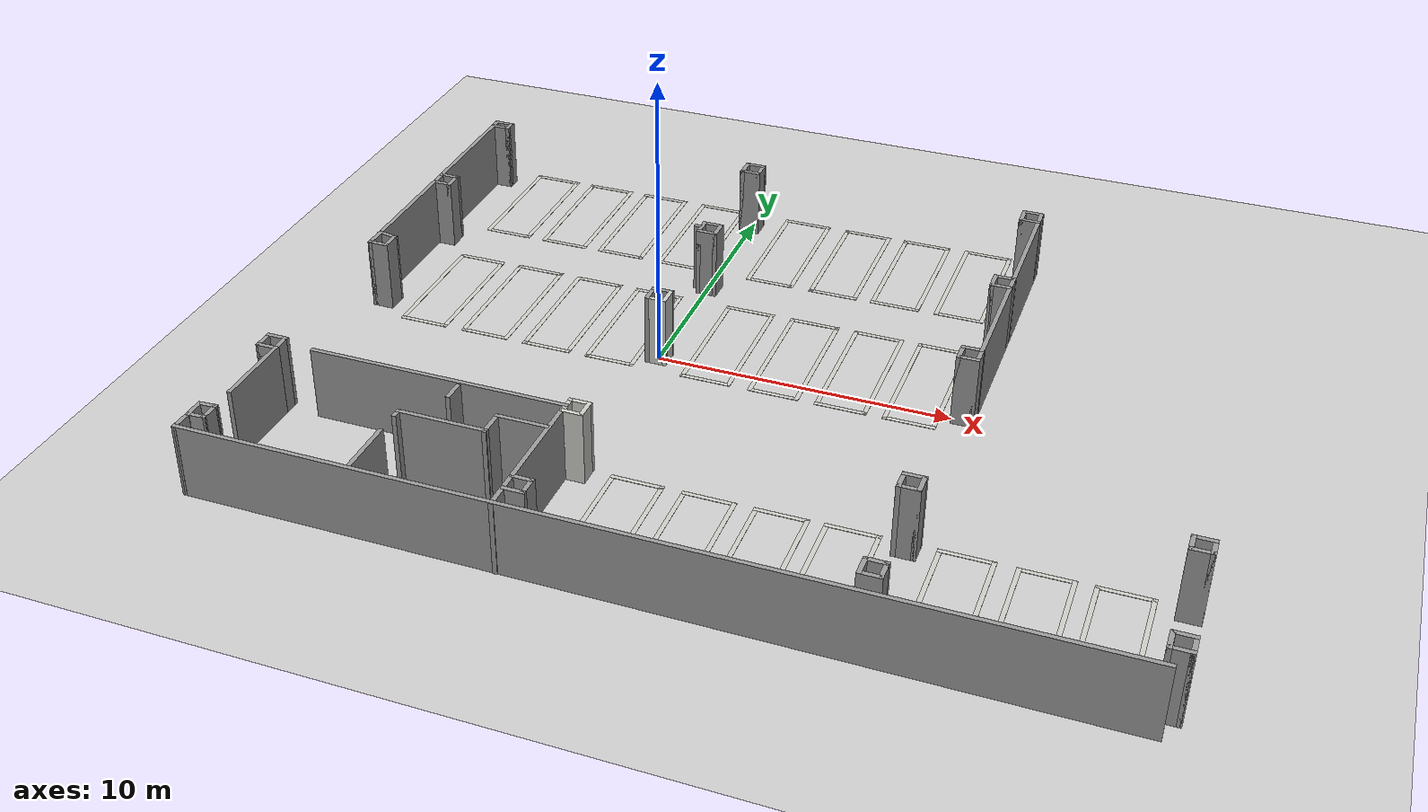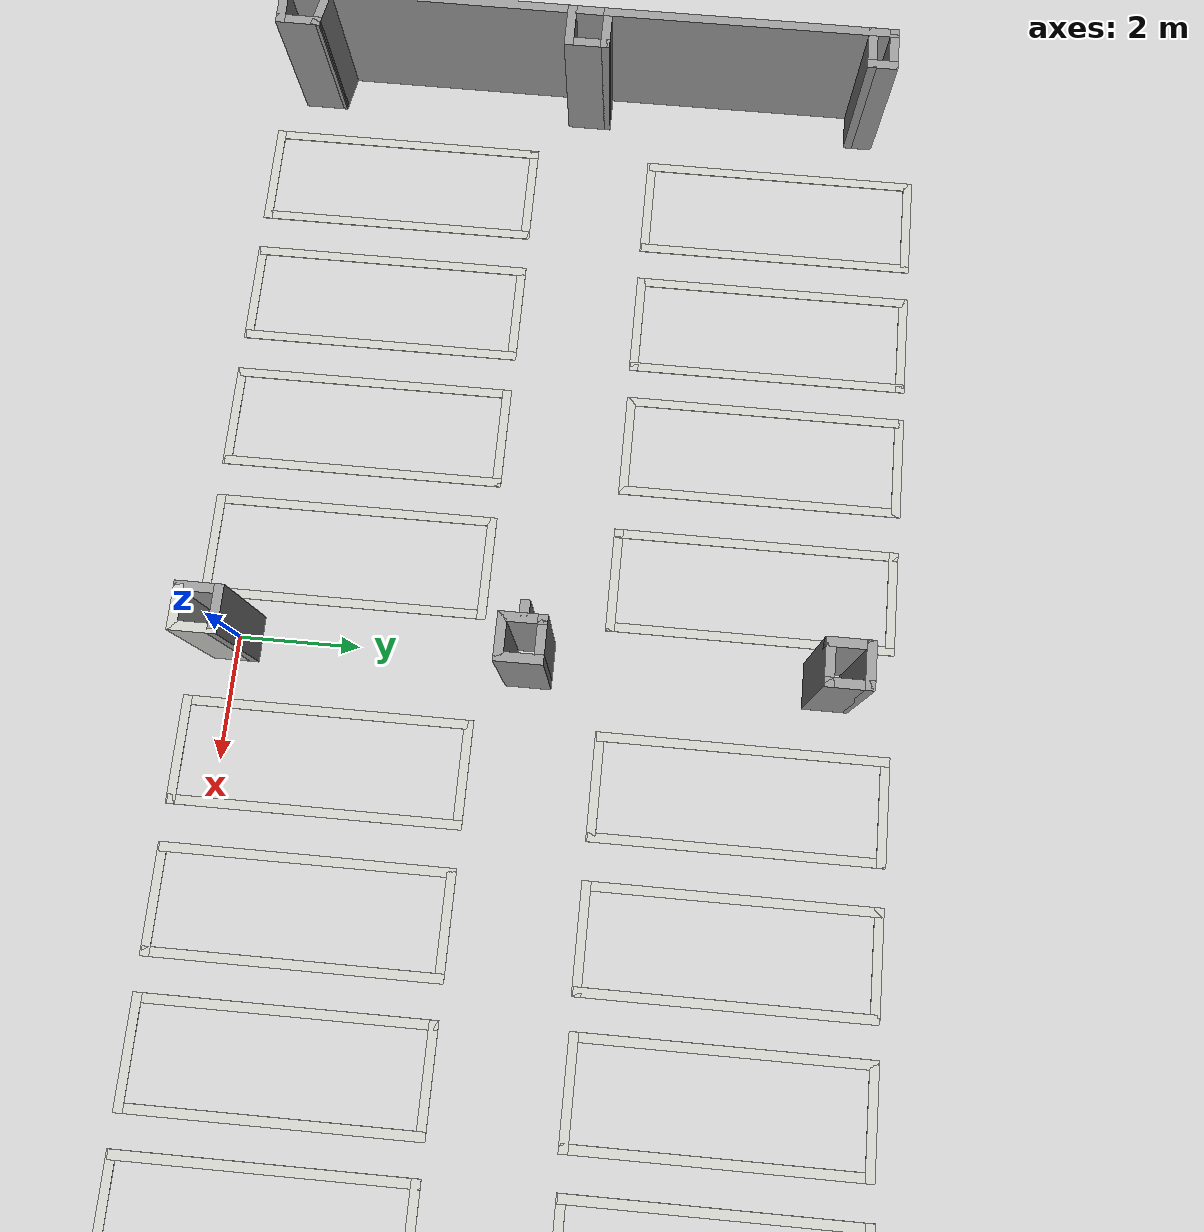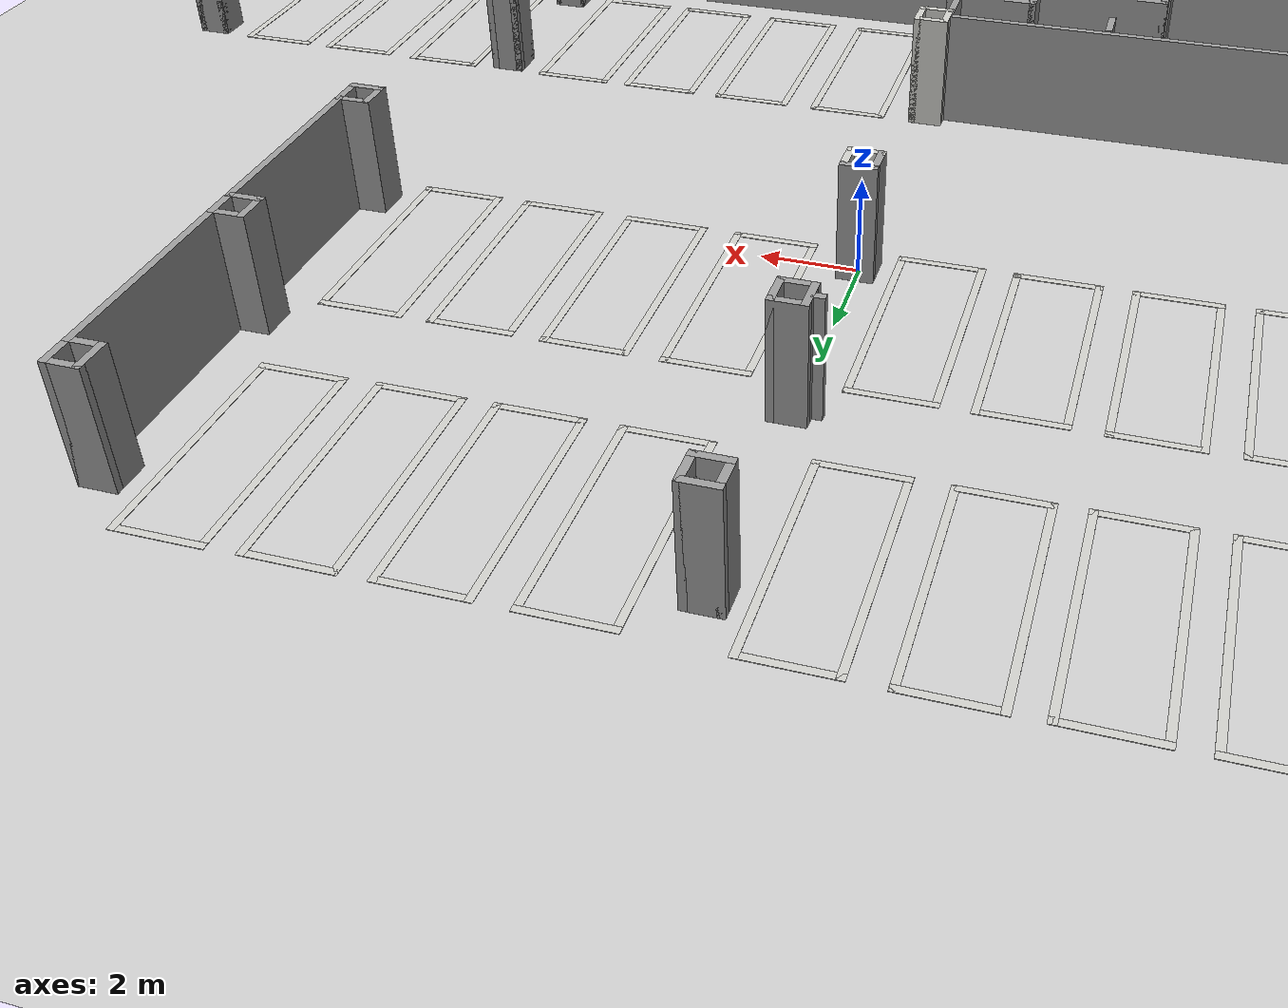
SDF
<sdf version="1.6">
 <world name="default">
  <light name="sun" type="directional">
   <pose>0 0 10 0 -0 0</pose>
   <diffuse>0.8 0.8 0.8 1</diffuse>
   <specular>0.2 0.2 0.2 1</specular>
   <attenuation>
    <range>1000</range>
    <constant>0.9</constant>
    <linear>0.01</linear>
    <quadratic>0.001</quadratic>
   </attenuation>
   <direction>-0.5 0.1 -0.9</direction>
  </light>
  <model name="ground_plane">
   <static>1</static>
   <link name="link">
    <collision name="collision">
     <geometry><plane><normal>0 0 1</normal><size>100 100</size></plane></geometry>
     <surface>
      <contact><collide_bitmask>65535</collide_bitmask></contact>
      <friction><ode><mu>100</mu><mu2>50</mu2></ode></friction>
     </surface>
    </collision>
    <visual name="visual">
     <cast_shadows>0</cast_shadows>
     <geometry><plane><normal>0 0 1</normal><size>100 100</size></plane></geometry>
     <material>
      <script><uri>file://media/materials/scripts/gazebo.material</uri><name>Gazebo/Grey</name></script>
     </material>
    </visual>
   </link>
  </model>
  <gravity>0 0 -9.8</gravity>
  <magnetic_field>6e-06 2.3e-05 -4.2e-05</magnetic_field>
  <atmosphere type="adiabatic"/>
  <physics name="default_physics" default="0" type="ode">
   <max_step_size>0.001</max_step_size>
   <real_time_factor>1</real_time_factor>
   <real_time_update_rate>1000</real_time_update_rate>
  </physics>
  <scene><ambient>0.4 0.4 0.4 1</ambient><background>0.7 0.7 0.7 1</background><shadows>1</shadows></scene>
  <audio><device>default</device></audio>
  <spherical_coordinates>
   <surface_model>EARTH_WGS84</surface_model>
   <latitude_deg>0</latitude_deg>
   <longitude_deg>0</longitude_deg>
   <elevation>0</elevation>
   <heading_deg>0</heading_deg>
  </spherical_coordinates>
  <model name="Untitled">
   <pose>4.02207 -1.0602 0 0 -0 0</pose>
   <link name="Wall_0">
    <collision name="Wall_0_Collision">
     <geometry><box><size>8.75 0.15 2.5</size></box></geometry>
     <pose>0 0 1.25 0 -0 0</pose>
    </collision>
    <visual name="Wall_0_Visual">
     <pose>0 0 1.25 0 -0 0</pose>
     <geometry><box><size>8.75 0.15 2.5</size></box></geometry>
     <material>
      <script><uri>file://media/materials/scripts/gazebo.material</uri><name>Gazebo/Grey</name></script>
      <ambient>1 1 1 1</ambient>
     </material>
     <meta><layer>0</layer></meta>
    </visual>
    <pose>-8.60497 -5.92583 0 0 -0 0</pose>
   </link>
   <link name="Wall_10">
    <collision name="Wall_10_Collision">
     <geometry><box><size>3 0.15 2.5</size></box></geometry>
     <pose>0 0 1.25 0 -0 0</pose>
    </collision>
    <visual name="Wall_10_Visual">
     <pose>0 0 1.25 0 -0 0</pose>
     <geometry><box><size>3 0.15 2.5</size></box></geometry>
     <material>
      <script><uri>file://media/materials/scripts/gazebo.material</uri><name>Gazebo/Grey</name></script>
      <ambient>1 1 1 1</ambient>
     </material>
     <meta><layer>0</layer></meta>
    </visual>
    <pose>-7.39897 -7.96447 0 0 -0 0</pose>
   </link>
   <link name="Wall_100">
    <collision name="Wall_100_Collision">
     <geometry><box><size>0.75 0.15 2.5</size></box></geometry>
     <pose>0 0 1.25 0 -0 0</pose>
    </collision>
    <visual name="Wall_100_Visual">
     <pose>0 0 1.25 0 -0 0</pose>
     <geometry><box><size>0.75 0.15 2.5</size></box></geometry>
     <material>
      <script><uri>file://media/materials/scripts/gazebo.material</uri><name>Gazebo/Grey</name></script>
      <ambient>1 1 1 1</ambient>
     </material>
     <meta><layer>0</layer></meta>
    </visual>
    <pose>6.05694 1.18506 0 0 -0 -1.5708</pose>
   </link>
   <link name="Wall_101">
    <collision name="Wall_101_Collision">
     <geometry><box><size>0.75 0.15 2.5</size></box></geometry>
     <pose>0 0 1.25 0 -0 0</pose>
    </collision>
    <visual name="Wall_101_Visual">
     <pose>0 0 1.25 0 -0 0</pose>
     <geometry><box><size>0.75 0.15 2.5</size></box></geometry>
     <material>
      <script><uri>file://media/materials/scripts/gazebo.material</uri><name>Gazebo/Grey</name></script>
      <ambient>1 1 1 1</ambient>
     </material>
     <meta><layer>0</layer></meta>
    </visual>
    <pose>6.35695 0.885058 0 0 -0 0</pose>
   </link>
   <link name="Wall_102">
    <collision name="Wall_102_Collision">
     <geometry><box><size>0.75 0.15 2.5</size></box></geometry>
     <pose>0 0 1.25 0 -0 0</pose>
    </collision>
    <visual name="Wall_102_Visual">
     <pose>0 0 1.25 0 -0 0</pose>
     <geometry><box><size>0.75 0.15 2.5</size></box></geometry>
     <material>
      <script><uri>file://media/materials/scripts/gazebo.material</uri><name>Gazebo/Grey</name></script>
      <ambient>1 1 1 1</ambient>
     </material>
     <meta><layer>0</layer></meta>
    </visual>
    <pose>6.65695 1.18506 0 0 -0 1.5708</pose>
   </link>
   <link name="Wall_108">
    <collision name="Wall_108_Collision">
     <geometry><box><size>0.75 0.15 2.5</size></box></geometry>
     <pose>0 0 1.25 0 -0 0</pose>
    </collision>
    <visual name="Wall_108_Visual">
     <pose>0 0 1.25 0 -0 0</pose>
     <geometry><box><size>0.75 0.15 2.5</size></box></geometry>
     <material>
      <script><uri>file://media/materials/scripts/gazebo.material</uri><name>Gazebo/Grey</name></script>
      <ambient>1 1 1 1</ambient>
     </material>
     <meta><layer>0</layer></meta>
    </visual>
    <pose>6.02979 -5.94295 0 0 -0 -1.5708</pose>
   </link>
   <link name="Wall_109">
    <collision name="Wall_109_Collision">
     <geometry><box><size>0.75 0.15 2.5</size></box></geometry>
     <pose>0 0 1.25 0 -0 0</pose>
    </collision>
    <visual name="Wall_109_Visual">
     <pose>0 0 1.25 0 -0 0</pose>
     <geometry><box><size>0.75 0.15 2.5</size></box></geometry>
     <material>
      <script><uri>file://media/materials/scripts/gazebo.material</uri><name>Gazebo/Grey</name></script>
      <ambient>1 1 1 1</ambient>
     </material>
     <meta><layer>0</layer></meta>
    </visual>
    <pose>6.32979 -6.24295 0 0 -0 0</pose>
   </link>
   <link name="Wall_110">
    <collision name="Wall_110_Collision">
     <geometry><box><size>0.75 0.15 2.5</size></box></geometry>
     <pose>0 0 1.25 0 -0 0</pose>
    </collision>
    <visual name="Wall_110_Visual">
     <pose>0 0 1.25 0 -0 0</pose>
     <geometry><box><size>0.75 0.15 2.5</size></box></geometry>
     <material>
      <script><uri>file://media/materials/scripts/gazebo.material</uri><name>Gazebo/Grey</name></script>
      <ambient>1 1 1 1</ambient>
     </material>
     <meta><layer>0</layer></meta>
    </visual>
    <pose>6.62979 -5.94295 0 0 -0 1.5708</pose>
   </link>
   <link name="Wall_111">
    <collision name="Wall_111_Collision">
     <geometry><box><size>0.75 0.15 2.5</size></box></geometry>
     <pose>0 0 1.25 0 -0 0</pose>
    </collision>
    <visual name="Wall_111_Visual">
     <pose>0 0 1.25 0 -0 0</pose>
     <geometry><box><size>0.75 0.15 2.5</size></box></geometry>
     <material>
      <script><uri>file://media/materials/scripts/gazebo.material</uri><name>Gazebo/Grey</name></script>
      <ambient>1 1 1 1</ambient>
     </material>
     <meta><layer>0</layer></meta>
    </visual>
    <pose>6.32979 -5.64295 0 0 -0 3.14159</pose>
   </link>
   <link name="Wall_116">
    <collision name="Wall_116_Collision">
     <geometry><box><size>0.75 0.15 2.5</size></box></geometry>
     <pose>0 0 1.25 0 -0 0</pose>
    </collision>
    <visual name="Wall_116_Visual">
     <pose>0 0 1.25 0 -0 0</pose>
     <geometry><box><size>0.75 0.15 2.5</size></box></geometry>
     <material>
      <script><uri>file://media/materials/scripts/gazebo.material</uri><name>Gazebo/Grey</name></script>
      <ambient>1 1 1 1</ambient>
     </material>
     <meta><layer>0</layer></meta>
    </visual>
    <pose>6.02979 -9.98578 0 0 -0 -1.5708</pose>
   </link>
   <link name="Wall_117">
    <collision name="Wall_117_Collision">
     <geometry><box><size>0.75 0.15 2.5</size></box></geometry>
     <pose>0 0 1.25 0 -0 0</pose>
    </collision>
    <visual name="Wall_117_Visual">
     <pose>0 0 1.25 0 -0 0</pose>
     <geometry><box><size>0.75 0.15 2.5</size></box></geometry>
     <material>
      <script><uri>file://media/materials/scripts/gazebo.material</uri><name>Gazebo/Grey</name></script>
      <ambient>1 1 1 1</ambient>
     </material>
     <meta><layer>0</layer></meta>
    </visual>
    <pose>6.32979 -10.2858 0 0 -0 0</pose>
   </link>
   <link name="Wall_118">
    <collision name="Wall_118_Collision">
     <geometry><box><size>0.75 0.15 2.5</size></box></geometry>
     <pose>0 0 1.25 0 -0 0</pose>
    </collision>
    <visual name="Wall_118_Visual">
     <pose>0 0 1.25 0 -0 0</pose>
     <geometry><box><size>0.75 0.15 2.5</size></box></geometry>
     <material>
      <script><uri>file://media/materials/scripts/gazebo.material</uri><name>Gazebo/Grey</name></script>
      <ambient>1 1 1 1</ambient>
     </material>
     <meta><layer>0</layer></meta>
    </visual>
    <pose>6.62979 -9.98578 0 0 -0 1.5708</pose>
   </link>
   <link name="Wall_119">
    <collision name="Wall_119_Collision">
     <geometry><box><size>0.75 0.15 2.5</size></box></geometry>
     <pose>0 0 1.25 0 -0 0</pose>
    </collision>
    <visual name="Wall_119_Visual">
     <pose>0 0 1.25 0 -0 0</pose>
     <geometry><box><size>0.75 0.15 2.5</size></box></geometry>
     <material>
      <script><uri>file://media/materials/scripts/gazebo.material</uri><name>Gazebo/Grey</name></script>
      <ambient>1 1 1 1</ambient>
     </material>
     <meta><layer>0</layer></meta>
    </visual>
    <pose>6.32979 -9.68578 0 0 -0 3.14159</pose>
   </link>
   <link name="Wall_12">
    <collision name="Wall_12_Collision">
     <geometry><box><size>0.75 0.15 2.5</size></box></geometry>
     <pose>0 0 1.25 0 -0 0</pose>
    </collision>
    <visual name="Wall_12_Visual">
     <pose>0 0 1.25 0 -0 0</pose>
     <geometry><box><size>0.75 0.15 2.5</size></box></geometry>
     <material>
      <script><uri>file://media/materials/scripts/gazebo.material</uri><name>Gazebo/Grey</name></script>
      <ambient>1 1 1 1</ambient>
     </material>
     <meta><layer>0</layer></meta>
    </visual>
    <pose>-7.78656 -6.44086 0 0 -0 1.5708</pose>
   </link>
   <link name="Wall_124">
    <collision name="Wall_124_Collision">
     <geometry><box><size>0.75 0.15 2.5</size></box></geometry>
     <pose>0 0 1.25 0 -0 0</pose>
    </collision>
    <visual name="Wall_124_Visual">
     <pose>0 0 1.25 0 -0 0</pose>
     <geometry><box><size>0.75 0.15 2.5</size></box></geometry>
     <material>
      <script><uri>file://media/materials/scripts/gazebo.material</uri><name>Gazebo/Grey</name></script>
      <ambient>1 1 1 1</ambient>
     </material>
     <meta><layer>0</layer></meta>
    </visual>
    <pose>-4.33544 10.7235 0 0 -0 -1.5708</pose>
   </link>
   <link name="Wall_125">
    <collision name="Wall_125_Collision">
     <geometry><box><size>0.75 0.15 2.5</size></box></geometry>
     <pose>0 0 1.25 0 -0 0</pose>
    </collision>
    <visual name="Wall_125_Visual">
     <pose>0 0 1.25 0 -0 0</pose>
     <geometry><box><size>0.75 0.15 2.5</size></box></geometry>
     <material>
      <script><uri>file://media/materials/scripts/gazebo.material</uri><name>Gazebo/Grey</name></script>
      <ambient>1 1 1 1</ambient>
     </material>
     <meta><layer>0</layer></meta>
    </visual>
    <pose>-4.03544 10.4235 0 0 -0 0</pose>
   </link>
   <link name="Wall_126">
    <collision name="Wall_126_Collision">
     <geometry><box><size>0.75 0.15 2.5</size></box></geometry>
     <pose>0 0 1.25 0 -0 0</pose>
    </collision>
    <visual name="Wall_126_Visual">
     <pose>0 0 1.25 0 -0 0</pose>
     <geometry><box><size>0.75 0.15 2.5</size></box></geometry>
     <material>
      <script><uri>file://media/materials/scripts/gazebo.material</uri><name>Gazebo/Grey</name></script>
      <ambient>1 1 1 1</ambient>
     </material>
     <meta><layer>0</layer></meta>
    </visual>
    <pose>-3.73544 10.7235 0 0 -0 1.5708</pose>
   </link>
   <link name="Wall_127">
    <collision name="Wall_127_Collision">
     <geometry><box><size>0.75 0.15 2.5</size></box></geometry>
     <pose>0 0 1.25 0 -0 0</pose>
    </collision>
    <visual name="Wall_127_Visual">
     <pose>0 0 1.25 0 -0 0</pose>
     <geometry><box><size>0.75 0.15 2.5</size></box></geometry>
     <material>
      <script><uri>file://media/materials/scripts/gazebo.material</uri><name>Gazebo/Grey</name></script>
      <ambient>1 1 1 1</ambient>
     </material>
     <meta><layer>0</layer></meta>
    </visual>
    <pose>-4.03544 11.0235 0 0 -0 3.14159</pose>
   </link>
   <link name="Wall_129">
    <collision name="Wall_129_Collision">
     <geometry><box><size>0.75 0.15 2.5</size></box></geometry>
     <pose>0 0 1.25 0 -0 0</pose>
    </collision>
    <visual name="Wall_129_Visual">
     <pose>0 0 1.25 0 -0 0</pose>
     <geometry><box><size>0.75 0.15 2.5</size></box></geometry>
     <material>
      <script><uri>file://media/materials/scripts/gazebo.material</uri><name>Gazebo/Grey</name></script>
      <ambient>1 1 1 1</ambient>
     </material>
     <meta><layer>0</layer></meta>
    </visual>
    <pose>6.03693 10.6931 0 0 -0 -1.5708</pose>
   </link>
   <link name="Wall_130">
    <collision name="Wall_130_Collision">
     <geometry><box><size>0.75 0.15 2.5</size></box></geometry>
     <pose>0 0 1.25 0 -0 0</pose>
    </collision>
    <visual name="Wall_130_Visual">
     <pose>0 0 1.25 0 -0 0</pose>
     <geometry><box><size>0.75 0.15 2.5</size></box></geometry>
     <material>
      <script><uri>file://media/materials/scripts/gazebo.material</uri><name>Gazebo/Grey</name></script>
      <ambient>1 1 1 1</ambient>
     </material>
     <meta><layer>0</layer></meta>
    </visual>
    <pose>6.33693 10.3931 0 0 -0 0</pose>
   </link>
   <link name="Wall_131">
    <collision name="Wall_131_Collision">
     <geometry><box><size>0.75 0.15 2.5</size></box></geometry>
     <pose>0 0 1.25 0 -0 0</pose>
    </collision>
    <visual name="Wall_131_Visual">
     <pose>0 0 1.25 0 -0 0</pose>
     <geometry><box><size>0.75 0.15 2.5</size></box></geometry>
     <material>
      <script><uri>file://media/materials/scripts/gazebo.material</uri><name>Gazebo/Grey</name></script>
      <ambient>1 1 1 1</ambient>
     </material>
     <meta><layer>0</layer></meta>
    </visual>
    <pose>6.63693 10.6931 0 0 -0 1.5708</pose>
   </link>
   <link name="Wall_132">
    <collision name="Wall_132_Collision">
     <geometry><box><size>0.75 0.15 2.5</size></box></geometry>
     <pose>0 0 1.25 0 -0 0</pose>
    </collision>
    <visual name="Wall_132_Visual">
     <pose>0 0 1.25 0 -0 0</pose>
     <geometry><box><size>0.75 0.15 2.5</size></box></geometry>
     <material>
      <script><uri>file://media/materials/scripts/gazebo.material</uri><name>Gazebo/Grey</name></script>
      <ambient>1 1 1 1</ambient>
     </material>
     <meta><layer>0</layer></meta>
    </visual>
    <pose>6.33693 10.9931 0 0 -0 3.14159</pose>
   </link>
   <link name="Wall_134">
    <collision name="Wall_134_Collision">
     <geometry><box><size>4.35811 0.15 2.5</size></box></geometry>
     <pose>0 0 1.25 0 -0 0</pose>
    </collision>
    <visual name="Wall_134_Visual">
     <pose>0 0 1.25 0 -0 0</pose>
     <geometry><box><size>4.35811 0.15 2.5</size></box></geometry>
     <material>
      <script><uri>file://media/materials/scripts/gazebo.material</uri><name>Gazebo/Grey</name></script>
      <ambient>1 1 1 1</ambient>
     </material>
     <meta><layer>0</layer></meta>
    </visual>
    <pose>6.64694 8.28909 0 0 -0 -1.56604</pose>
   </link>
   <link name="Wall_14">
    <collision name="Wall_14_Collision">
     <geometry><box><size>0.815537 0.15 2.5</size></box></geometry>
     <pose>0 0 1.25 0 -0 0</pose>
    </collision>
    <visual name="Wall_14_Visual">
     <pose>0 0 1.25 0 -0 0</pose>
     <geometry><box><size>0.815537 0.15 2.5</size></box></geometry>
     <material>
      <script><uri>file://media/materials/scripts/gazebo.material</uri><name>Gazebo/Grey</name></script>
      <ambient>1 1 1 1</ambient>
     </material>
     <meta><layer>0</layer></meta>
    </visual>
    <pose>-14.5829 -10.6644 0 0 -0 -1.61078</pose>
   </link>
   <link name="Wall_140">
    <collision name="Wall_140_Collision">
     <geometry><box><size>0.6968 0.15 2.5</size></box></geometry>
     <pose>0 0 1.25 0 -0 0</pose>
    </collision>
    <visual name="Wall_140_Visual">
     <pose>0 0 1.25 0 -0 0</pose>
     <geometry><box><size>0.6968 0.15 2.5</size></box></geometry>
     <material>
      <script><uri>file://media/materials/scripts/gazebo.material</uri><name>Gazebo/Grey</name></script>
      <ambient>1 1 1 1</ambient>
     </material>
     <meta><layer>0</layer></meta>
    </visual>
    <pose>14.0546 -5.90185 0 0 -0 -1.5708</pose>
   </link>
   <link name="Wall_143">
    <collision name="Wall_143_Collision">
     <geometry><box><size>0.75 0.15 2.5</size></box></geometry>
     <pose>0 0 1.25 0 -0 0</pose>
    </collision>
    <visual name="Wall_143_Visual">
     <pose>0 0 1.25 0 -0 0</pose>
     <geometry><box><size>0.75 0.15 2.5</size></box></geometry>
     <material>
      <script><uri>file://media/materials/scripts/gazebo.material</uri><name>Gazebo/Grey</name></script>
      <ambient>1 1 1 1</ambient>
     </material>
     <meta><layer>0</layer></meta>
    </visual>
    <pose>14.3546 -6.17525 0 0 -0 0</pose>
   </link>
   <link name="Wall_144">
    <collision name="Wall_144_Collision">
     <geometry><box><size>0.6968 0.15 2.5</size></box></geometry>
     <pose>0 0 1.25 0 -0 0</pose>
    </collision>
    <visual name="Wall_144_Visual">
     <pose>0 0 1.25 0 -0 0</pose>
     <geometry><box><size>0.6968 0.15 2.5</size></box></geometry>
     <material>
      <script><uri>file://media/materials/scripts/gazebo.material</uri><name>Gazebo/Grey</name></script>
      <ambient>1 1 1 1</ambient>
     </material>
     <meta><layer>0</layer></meta>
    </visual>
    <pose>14.6546 -5.90185 0 0 -0 1.5708</pose>
   </link>
   <link name="Wall_145">
    <collision name="Wall_145_Collision">
     <geometry><box><size>0.75 0.15 2.5</size></box></geometry>
     <pose>0 0 1.25 0 -0 0</pose>
    </collision>
    <visual name="Wall_145_Visual">
     <pose>0 0 1.25 0 -0 0</pose>
     <geometry><box><size>0.75 0.15 2.5</size></box></geometry>
     <material>
      <script><uri>file://media/materials/scripts/gazebo.material</uri><name>Gazebo/Grey</name></script>
      <ambient>1 1 1 1</ambient>
     </material>
     <meta><layer>0</layer></meta>
    </visual>
    <pose>14.3546 -5.62845 0 0 -0 3.14159</pose>
   </link>
   <link name="Wall_154">
    <collision name="Wall_154_Collision">
     <geometry><box><size>0.75 0.15 2.5</size></box></geometry>
     <pose>0 0 1.25 0 -0 0</pose>
    </collision>
    <visual name="Wall_154_Visual">
     <pose>0 0 1.25 0 -0 0</pose>
     <geometry><box><size>0.75 0.15 2.5</size></box></geometry>
     <material>
      <script><uri>file://media/materials/scripts/gazebo.material</uri><name>Gazebo/Grey</name></script>
      <ambient>1 1 1 1</ambient>
     </material>
     <meta><layer>0</layer></meta>
    </visual>
    <pose>14.0691 -10.0298 0 0 -0 -1.5708</pose>
   </link>
   <link name="Wall_155">
    <collision name="Wall_155_Collision">
     <geometry><box><size>0.75 0.15 2.5</size></box></geometry>
     <pose>0 0 1.25 0 -0 0</pose>
    </collision>
    <visual name="Wall_155_Visual">
     <pose>0 0 1.25 0 -0 0</pose>
     <geometry><box><size>0.75 0.15 2.5</size></box></geometry>
     <material>
      <script><uri>file://media/materials/scripts/gazebo.material</uri><name>Gazebo/Grey</name></script>
      <ambient>1 1 1 1</ambient>
     </material>
     <meta><layer>0</layer></meta>
    </visual>
    <pose>14.3691 -10.3298 0 0 -0 0</pose>
   </link>
   <link name="Wall_156">
    <collision name="Wall_156_Collision">
     <geometry><box><size>0.75 0.15 2.5</size></box></geometry>
     <pose>0 0 1.25 0 -0 0</pose>
    </collision>
    <visual name="Wall_156_Visual">
     <pose>0 0 1.25 0 -0 0</pose>
     <geometry><box><size>0.75 0.15 2.5</size></box></geometry>
     <material>
      <script><uri>file://media/materials/scripts/gazebo.material</uri><name>Gazebo/Grey</name></script>
      <ambient>1 1 1 1</ambient>
     </material>
     <meta><layer>0</layer></meta>
    </visual>
    <pose>14.6691 -10.0298 0 0 -0 1.5708</pose>
   </link>
   <link name="Wall_157">
    <collision name="Wall_157_Collision">
     <geometry><box><size>0.75 0.15 2.5</size></box></geometry>
     <pose>0 0 1.25 0 -0 0</pose>
    </collision>
    <visual name="Wall_157_Visual">
     <pose>0 0 1.25 0 -0 0</pose>
     <geometry><box><size>0.75 0.15 2.5</size></box></geometry>
     <material>
      <script><uri>file://media/materials/scripts/gazebo.material</uri><name>Gazebo/Grey</name></script>
      <ambient>1 1 1 1</ambient>
     </material>
     <meta><layer>0</layer></meta>
    </visual>
    <pose>14.3691 -9.72985 0 0 -0 3.14159</pose>
   </link>
   <link name="Wall_16">
    <collision name="Wall_16_Collision">
     <geometry><box><size>2 0.15 2.5</size></box></geometry>
     <pose>0 0 1.25 0 -0 0</pose>
    </collision>
    <visual name="Wall_16_Visual">
     <pose>0 0 1.25 0 -0 0</pose>
     <geometry><box><size>2 0.15 2.5</size></box></geometry>
     <material>
      <script><uri>file://media/materials/scripts/gazebo.material</uri><name>Gazebo/Grey</name></script>
      <ambient>1 1 1 1</ambient>
     </material>
     <meta><layer>0</layer></meta>
    </visual>
    <pose>-8.84658 -9.98672 0 0 -0 -1.5708</pose>
   </link>
   <link name="Wall_18">
    <collision name="Wall_18_Collision">
     <geometry><box><size>0.389402 0.15 2.5</size></box></geometry>
     <pose>0 0 1.25 0 -0 0</pose>
    </collision>
    <visual name="Wall_18_Visual">
     <pose>0 0 1.25 0 -0 0</pose>
     <geometry><box><size>0.389402 0.15 2.5</size></box></geometry>
     <material>
      <script><uri>file://media/materials/scripts/gazebo.material</uri><name>Gazebo/Grey</name></script>
      <ambient>1 1 1 1</ambient>
     </material>
     <meta><layer>0</layer></meta>
    </visual>
    <pose>-8.82397 -8.08417 0 0 -0 1.5708</pose>
   </link>
   <link name="Wall_20">
    <collision name="Wall_20_Collision">
     <geometry><box><size>1 0.15 2.5</size></box></geometry>
     <pose>0 0 1.25 0 -0 0</pose>
    </collision>
    <visual name="Wall_20_Visual">
     <pose>0 0 1.25 0 -0 0</pose>
     <geometry><box><size>1 0.15 2.5</size></box></geometry>
     <material>
      <script><uri>file://media/materials/scripts/gazebo.material</uri><name>Gazebo/Grey</name></script>
      <ambient>1 1 1 1</ambient>
     </material>
     <meta><layer>0</layer></meta>
    </visual>
    <pose>-5.97775 -7.56607 0 0 -0 1.5708</pose>
   </link>
   <link name="Wall_21">
    <collision name="Wall_21_Collision">
     <geometry><box><size>1.75 0.15 2.5</size></box></geometry>
     <pose>0 0 1.25 0 -0 0</pose>
    </collision>
    <visual name="Wall_21_Visual">
     <pose>0 0 1.25 0 -0 0</pose>
     <geometry><box><size>1.75 0.15 2.5</size></box></geometry>
     <material>
      <script><uri>file://media/materials/scripts/gazebo.material</uri><name>Gazebo/Grey</name></script>
      <ambient>1 1 1 1</ambient>
     </material>
     <meta><layer>0</layer></meta>
    </visual>
    <pose>-5.17775 -7.14107 0 0 -0 0</pose>
   </link>
   <link name="Wall_30">
    <collision name="Wall_30_Collision">
     <geometry><box><size>0.75 0.15 2.5</size></box></geometry>
     <pose>0 0 1.25 0 -0 0</pose>
    </collision>
    <visual name="Wall_30_Visual">
     <pose>0 0 1.25 0 -0 0</pose>
     <geometry><box><size>0.75 0.15 2.5</size></box></geometry>
     <material>
      <script><uri>file://media/materials/scripts/gazebo.material</uri><name>Gazebo/Grey</name></script>
      <ambient>1 1 1 1</ambient>
     </material>
     <meta><layer>0</layer></meta>
    </visual>
    <pose>-14.3691 -5.65192 0 0 -0 3.14159</pose>
   </link>
   <link name="Wall_31">
    <collision name="Wall_31_Collision">
     <geometry><box><size>0.75 0.15 2.5</size></box></geometry>
     <pose>0 0 1.25 0 -0 0</pose>
    </collision>
    <visual name="Wall_31_Visual">
     <pose>0 0 1.25 0 -0 0</pose>
     <geometry><box><size>0.75 0.15 2.5</size></box></geometry>
     <material>
      <script><uri>file://media/materials/scripts/gazebo.material</uri><name>Gazebo/Grey</name></script>
      <ambient>1 1 1 1</ambient>
     </material>
     <meta><layer>0</layer></meta>
    </visual>
    <pose>-14.6691 -5.95192 0 0 -0 -1.5708</pose>
   </link>
   <link name="Wall_32">
    <collision name="Wall_32_Collision">
     <geometry><box><size>0.75 0.15 2.5</size></box></geometry>
     <pose>0 0 1.25 0 -0 0</pose>
    </collision>
    <visual name="Wall_32_Visual">
     <pose>0 0 1.25 0 -0 0</pose>
     <geometry><box><size>0.75 0.15 2.5</size></box></geometry>
     <material>
      <script><uri>file://media/materials/scripts/gazebo.material</uri><name>Gazebo/Grey</name></script>
      <ambient>1 1 1 1</ambient>
     </material>
     <meta><layer>0</layer></meta>
    </visual>
    <pose>-14.3691 -6.25192 0 0 -0 0</pose>
   </link>
   <link name="Wall_33">
    <collision name="Wall_33_Collision">
     <geometry><box><size>0.75 0.15 2.5</size></box></geometry>
     <pose>0 0 1.25 0 -0 0</pose>
    </collision>
    <visual name="Wall_33_Visual">
     <pose>0 0 1.25 0 -0 0</pose>
     <geometry><box><size>0.75 0.15 2.5</size></box></geometry>
     <material>
      <script><uri>file://media/materials/scripts/gazebo.material</uri><name>Gazebo/Grey</name></script>
      <ambient>1 1 1 1</ambient>
     </material>
     <meta><layer>0</layer></meta>
    </visual>
    <pose>-14.0691 -5.95192 0 0 -0 1.5708</pose>
   </link>
   <link name="Wall_35">
    <collision name="Wall_35_Collision">
     <geometry><box><size>2.75 0.15 2.5</size></box></geometry>
     <pose>0 0 1.25 0 -0 0</pose>
    </collision>
    <visual name="Wall_35_Visual">
     <pose>0 0 1.25 0 -0 0</pose>
     <geometry><box><size>2.75 0.15 2.5</size></box></geometry>
     <material>
      <script><uri>file://media/materials/scripts/gazebo.material</uri><name>Gazebo/Grey</name></script>
      <ambient>1 1 1 1</ambient>
     </material>
     <meta><layer>0</layer></meta>
    </visual>
    <pose>-14.0691 -7.55192 0 0 -0 -1.5708</pose>
   </link>
   <link name="Wall_37">
    <collision name="Wall_37_Collision">
     <geometry><box><size>0.75 0.15 2.5</size></box></geometry>
     <pose>0 0 1.25 0 -0 0</pose>
    </collision>
    <visual name="Wall_37_Visual">
     <pose>0 0 1.25 0 -0 0</pose>
     <geometry><box><size>0.75 0.15 2.5</size></box></geometry>
     <material>
      <script><uri>file://media/materials/scripts/gazebo.material</uri><name>Gazebo/Grey</name></script>
      <ambient>1 1 1 1</ambient>
     </material>
     <meta><layer>0</layer></meta>
    </visual>
    <pose>-14.0589 -9.99265 0 0 -0 -1.5708</pose>
   </link>
   <link name="Wall_38">
    <collision name="Wall_38_Collision">
     <geometry><box><size>0.662197 0.15 2.5</size></box></geometry>
     <pose>0 0 1.25 0 -0 0</pose>
    </collision>
    <visual name="Wall_38_Visual">
     <pose>0 0 1.25 0 -0 0</pose>
     <geometry><box><size>0.662197 0.15 2.5</size></box></geometry>
     <material>
      <script><uri>file://media/materials/scripts/gazebo.material</uri><name>Gazebo/Grey</name></script>
      <ambient>1 1 1 1</ambient>
     </material>
     <meta><layer>0</layer></meta>
    </visual>
    <pose>-14.3143 -10.3123 0 0 -0 -3.06492</pose>
   </link>
   <link name="Wall_39">
    <collision name="Wall_39_Collision">
     <geometry><box><size>0.75 0.15 2.5</size></box></geometry>
     <pose>0 0 1.25 0 -0 0</pose>
    </collision>
    <visual name="Wall_39_Visual">
     <pose>0 0 1.25 0 -0 0</pose>
     <geometry><box><size>0.75 0.15 2.5</size></box></geometry>
     <material>
      <script><uri>file://media/materials/scripts/gazebo.material</uri><name>Gazebo/Grey</name></script>
      <ambient>1 1 1 1</ambient>
     </material>
     <meta><layer>0</layer></meta>
    </visual>
    <pose>-14.5696 -10.0319 0 0 -0 1.5708</pose>
   </link>
   <link name="Wall_40">
    <collision name="Wall_40_Collision">
     <geometry><box><size>0.662197 0.15 2.5</size></box></geometry>
     <pose>0 0 1.25 0 -0 0</pose>
    </collision>
    <visual name="Wall_40_Visual">
     <pose>0 0 1.25 0 -0 0</pose>
     <geometry><box><size>0.662197 0.15 2.5</size></box></geometry>
     <material>
      <script><uri>file://media/materials/scripts/gazebo.material</uri><name>Gazebo/Grey</name></script>
      <ambient>1 1 1 1</ambient>
     </material>
     <meta><layer>0</layer></meta>
    </visual>
    <pose>-14.3143 -9.71227 0 0 -0 0.076675</pose>
   </link>
   <link name="Wall_42">
    <collision name="Wall_42_Collision">
     <geometry><box><size>0.75 0.15 2.5</size></box></geometry>
     <pose>0 0 1.25 0 -0 0</pose>
    </collision>
    <visual name="Wall_42_Visual">
     <pose>0 0 1.25 0 -0 0</pose>
     <geometry><box><size>0.75 0.15 2.5</size></box></geometry>
     <material>
      <script><uri>file://media/materials/scripts/gazebo.material</uri><name>Gazebo/CeilingTiled</name></script>
      <ambient>1 1 1 1</ambient>
     </material>
     <meta><layer>0</layer></meta>
    </visual>
    <pose>-4.27105 -5.89885 0 0 -0 -1.5708</pose>
   </link>
   <link name="Wall_43">
    <collision name="Wall_43_Collision">
     <geometry><box><size>0.75 0.15 2.5</size></box></geometry>
     <pose>0 0 1.25 0 -0 0</pose>
    </collision>
    <visual name="Wall_43_Visual">
     <pose>0 0 1.25 0 -0 0</pose>
     <geometry><box><size>0.75 0.15 2.5</size></box></geometry>
     <material>
      <script><uri>file://media/materials/scripts/gazebo.material</uri><name>Gazebo/CeilingTiled</name></script>
      <ambient>1 1 1 1</ambient>
     </material>
     <meta><layer>0</layer></meta>
    </visual>
    <pose>-3.97105 -6.19885 0 0 -0 0</pose>
   </link>
   <link name="Wall_44">
    <collision name="Wall_44_Collision">
     <geometry><box><size>0.75 0.15 2.5</size></box></geometry>
     <pose>0 0 1.25 0 -0 0</pose>
    </collision>
    <visual name="Wall_44_Visual">
     <pose>0 0 1.25 0 -0 0</pose>
     <geometry><box><size>0.75 0.15 2.5</size></box></geometry>
     <material>
      <script><uri>file://media/materials/scripts/gazebo.material</uri><name>Gazebo/CeilingTiled</name></script>
      <ambient>1 1 1 1</ambient>
     </material>
     <meta><layer>0</layer></meta>
    </visual>
    <pose>-3.67105 -5.89885 0 0 -0 1.5708</pose>
   </link>
   <link name="Wall_45">
    <collision name="Wall_45_Collision">
     <geometry><box><size>0.75 0.15 2.5</size></box></geometry>
     <pose>0 0 1.25 0 -0 0</pose>
    </collision>
    <visual name="Wall_45_Visual">
     <pose>0 0 1.25 0 -0 0</pose>
     <geometry><box><size>0.75 0.15 2.5</size></box></geometry>
     <material>
      <script><uri>file://media/materials/scripts/gazebo.material</uri><name>Gazebo/CeilingTiled</name></script>
      <ambient>1 1 1 1</ambient>
     </material>
     <meta><layer>0</layer></meta>
    </visual>
    <pose>-3.97105 -5.59885 0 0 -0 3.14159</pose>
   </link>
   <link name="Wall_47">
    <collision name="Wall_47_Collision">
     <geometry><box><size>0.75 0.15 2.5</size></box></geometry>
     <pose>0 0 1.25 0 -0 0</pose>
    </collision>
    <visual name="Wall_47_Visual">
     <pose>0 0 1.25 0 -0 0</pose>
     <geometry><box><size>0.75 0.15 2.5</size></box></geometry>
     <material>
      <script><uri>file://media/materials/scripts/gazebo.material</uri><name>Gazebo/Grey</name></script>
      <ambient>1 1 1 1</ambient>
     </material>
     <meta><layer>0</layer></meta>
    </visual>
    <pose>-3.9856 -9.69325 0 0 -0 0</pose>
   </link>
   <link name="Wall_48">
    <collision name="Wall_48_Collision">
     <geometry><box><size>0.75 0.15 2.5</size></box></geometry>
     <pose>0 0 1.25 0 -0 0</pose>
    </collision>
    <visual name="Wall_48_Visual">
     <pose>0 0 1.25 0 -0 0</pose>
     <geometry><box><size>0.75 0.15 2.5</size></box></geometry>
     <material>
      <script><uri>file://media/materials/scripts/gazebo.material</uri><name>Gazebo/Grey</name></script>
      <ambient>1 1 1 1</ambient>
     </material>
     <meta><layer>0</layer></meta>
    </visual>
    <pose>-3.6856 -9.99325 0 0 -0 -1.5708</pose>
   </link>
   <link name="Wall_49">
    <collision name="Wall_49_Collision">
     <geometry><box><size>0.75 0.15 2.5</size></box></geometry>
     <pose>0 0 1.25 0 -0 0</pose>
    </collision>
    <visual name="Wall_49_Visual">
     <pose>0 0 1.25 0 -0 0</pose>
     <geometry><box><size>0.75 0.15 2.5</size></box></geometry>
     <material>
      <script><uri>file://media/materials/scripts/gazebo.material</uri><name>Gazebo/Grey</name></script>
      <ambient>1 1 1 1</ambient>
     </material>
     <meta><layer>0</layer></meta>
    </visual>
    <pose>-3.9856 -10.2933 0 0 -0 3.14159</pose>
   </link>
   <link name="Wall_51">
    <collision name="Wall_51_Collision">
     <geometry><box><size>0.75 0.15 2.5</size></box></geometry>
     <pose>0 0 1.25 0 -0 0</pose>
    </collision>
    <visual name="Wall_51_Visual">
     <pose>0 0 1.25 0 -0 0</pose>
     <geometry><box><size>0.75 0.15 2.5</size></box></geometry>
     <material>
      <script><uri>file://media/materials/scripts/gazebo.material</uri><name>Gazebo/Grey</name></script>
      <ambient>1 1 1 1</ambient>
     </material>
     <meta><layer>0</layer></meta>
    </visual>
    <pose>-14.2804 0.814265 0 0 -0 0</pose>
   </link>
   <link name="Wall_52">
    <collision name="Wall_52_Collision">
     <geometry><box><size>0.75 0.15 2.5</size></box></geometry>
     <pose>0 0 1.25 0 -0 0</pose>
    </collision>
    <visual name="Wall_52_Visual">
     <pose>0 0 1.25 0 -0 0</pose>
     <geometry><box><size>0.75 0.15 2.5</size></box></geometry>
     <material>
      <script><uri>file://media/materials/scripts/gazebo.material</uri><name>Gazebo/Grey</name></script>
      <ambient>1 1 1 1</ambient>
     </material>
     <meta><layer>0</layer></meta>
    </visual>
    <pose>-13.9804 1.11427 0 0 -0 1.5708</pose>
   </link>
   <link name="Wall_53">
    <collision name="Wall_53_Collision">
     <geometry><box><size>0.7608 0.15 2.5</size></box></geometry>
     <pose>0 0 1.25 0 -0 0</pose>
    </collision>
    <visual name="Wall_53_Visual">
     <pose>0 0 1.25 0 -0 0</pose>
     <geometry><box><size>0.7608 0.15 2.5</size></box></geometry>
     <material>
      <script><uri>file://media/materials/scripts/gazebo.material</uri><name>Gazebo/Grey</name></script>
      <ambient>1 1 1 1</ambient>
     </material>
     <meta><layer>0</layer></meta>
    </visual>
    <pose>-14.2804 1.47144 0 0 -0 2.95327</pose>
   </link>
   <link name="Wall_54">
    <collision name="Wall_54_Collision">
     <geometry><box><size>0.864351 0.15 2.5</size></box></geometry>
     <pose>0 0 1.25 0 -0 0</pose>
    </collision>
    <visual name="Wall_54_Visual">
     <pose>0 0 1.25 0 -0 0</pose>
     <geometry><box><size>0.864351 0.15 2.5</size></box></geometry>
     <material>
      <script><uri>file://media/materials/scripts/gazebo.material</uri><name>Gazebo/Grey</name></script>
      <ambient>1 1 1 1</ambient>
     </material>
     <meta><layer>0</layer></meta>
    </visual>
    <pose>-14.5804 1.17144 0 0 -0 -1.5708</pose>
   </link>
   <link name="Wall_56">
    <collision name="Wall_56_Collision">
     <geometry><box><size>4.25 0.15 2.5</size></box></geometry>
     <pose>0 0 1.25 0 -0 0</pose>
    </collision>
    <visual name="Wall_56_Visual">
     <pose>0 0 1.25 0 -0 0</pose>
     <geometry><box><size>4.25 0.15 2.5</size></box></geometry>
     <material>
      <script><uri>file://media/materials/scripts/gazebo.material</uri><name>Gazebo/Grey</name></script>
      <ambient>1 1 1 1</ambient>
     </material>
     <meta><layer>0</layer></meta>
    </visual>
    <pose>-14.5804 3.56718 0 0 -0 1.5708</pose>
   </link>
   <link name="Wall_6">
    <collision name="Wall_6_Collision">
     <geometry><box><size>29 0.15 2.5</size></box></geometry>
     <pose>0 0 1.25 0 -0 0</pose>
    </collision>
    <visual name="Wall_6_Visual">
     <pose>0 0 1.25 0 -0 0</pose>
     <geometry><box><size>29 0.15 2.5</size></box></geometry>
     <material>
      <script><uri>file://media/materials/scripts/gazebo.material</uri><name>Gazebo/Grey</name></script>
      <ambient>1 1 1 1</ambient>
     </material>
     <meta><layer>0</layer></meta>
    </visual>
    <pose>-0.171213 -10.9969 0 0 -0 0</pose>
   </link>
   <link name="Wall_60">
    <collision name="Wall_60_Collision">
     <geometry><box><size>0.75 0.15 2.5</size></box></geometry>
     <pose>0 0 1.25 0 -0 0</pose>
    </collision>
    <visual name="Wall_60_Visual">
     <pose>0 0 1.25 0 -0 0</pose>
     <geometry><box><size>0.75 0.15 2.5</size></box></geometry>
     <material>
      <script><uri>file://media/materials/scripts/gazebo.material</uri><name>Gazebo/Grey</name></script>
      <ambient>1 1 1 1</ambient>
     </material>
     <meta><layer>0</layer></meta>
    </visual>
    <pose>-14.2804 5.61718 0 0 -0 0</pose>
   </link>
   <link name="Wall_61">
    <collision name="Wall_61_Collision">
     <geometry><box><size>0.75 0.15 2.5</size></box></geometry>
     <pose>0 0 1.25 0 -0 0</pose>
    </collision>
    <visual name="Wall_61_Visual">
     <pose>0 0 1.25 0 -0 0</pose>
     <geometry><box><size>0.75 0.15 2.5</size></box></geometry>
     <material>
      <script><uri>file://media/materials/scripts/gazebo.material</uri><name>Gazebo/Grey</name></script>
      <ambient>1 1 1 1</ambient>
     </material>
     <meta><layer>0</layer></meta>
    </visual>
    <pose>-13.9804 5.91718 0 0 -0 1.5708</pose>
   </link>
   <link name="Wall_62">
    <collision name="Wall_62_Collision">
     <geometry><box><size>0.75 0.15 2.5</size></box></geometry>
     <pose>0 0 1.25 0 -0 0</pose>
    </collision>
    <visual name="Wall_62_Visual">
     <pose>0 0 1.25 0 -0 0</pose>
     <geometry><box><size>0.75 0.15 2.5</size></box></geometry>
     <material>
      <script><uri>file://media/materials/scripts/gazebo.material</uri><name>Gazebo/Grey</name></script>
      <ambient>1 1 1 1</ambient>
     </material>
     <meta><layer>0</layer></meta>
    </visual>
    <pose>-14.2804 6.21718 0 0 -0 3.14159</pose>
   </link>
   <link name="Wall_63">
    <collision name="Wall_63_Collision">
     <geometry><box><size>0.75 0.15 2.5</size></box></geometry>
     <pose>0 0 1.25 0 -0 0</pose>
    </collision>
    <visual name="Wall_63_Visual">
     <pose>0 0 1.25 0 -0 0</pose>
     <geometry><box><size>0.75 0.15 2.5</size></box></geometry>
     <material>
      <script><uri>file://media/materials/scripts/gazebo.material</uri><name>Gazebo/Grey</name></script>
      <ambient>1 1 1 1</ambient>
     </material>
     <meta><layer>0</layer></meta>
    </visual>
    <pose>-14.5804 5.91718 0 0 -0 -1.5708</pose>
   </link>
   <link name="Wall_65">
    <collision name="Wall_65_Collision">
     <geometry><box><size>4.89778 0.15 2.5</size></box></geometry>
     <pose>0 0 1.25 0 -0 0</pose>
    </collision>
    <visual name="Wall_65_Visual">
     <pose>0 0 1.25 0 -0 0</pose>
     <geometry><box><size>4.89778 0.15 2.5</size></box></geometry>
     <material>
      <script><uri>file://media/materials/scripts/gazebo.material</uri><name>Gazebo/Grey</name></script>
      <ambient>1 1 1 1</ambient>
     </material>
     <meta><layer>0</layer></meta>
    </visual>
    <pose>-14.5886 8.59106 0 0 -0 -1.56735</pose>
   </link>
   <link name="Wall_69">
    <collision name="Wall_69_Collision">
     <geometry><box><size>0.75 0.15 2.5</size></box></geometry>
     <pose>0 0 1.25 0 -0 0</pose>
    </collision>
    <visual name="Wall_69_Visual">
     <pose>0 0 1.25 0 -0 0</pose>
     <geometry><box><size>0.75 0.15 2.5</size></box></geometry>
     <material>
      <script><uri>file://media/materials/scripts/gazebo.material</uri><name>Gazebo/Grey</name></script>
      <ambient>1 1 1 1</ambient>
     </material>
     <meta><layer>0</layer></meta>
    </visual>
    <pose>-14.2968 10.9649 0 0 -0 0</pose>
   </link>
   <link name="Wall_72">
    <collision name="Wall_72_Collision">
     <geometry><box><size>0.5 0.15 2.5</size></box></geometry>
     <pose>0 0 1.25 0 -0 0</pose>
    </collision>
    <visual name="Wall_72_Visual">
     <pose>0 0 1.25 0 -0 0</pose>
     <geometry><box><size>0.5 0.15 2.5</size></box></geometry>
     <material>
      <script><uri>file://media/materials/scripts/gazebo.material</uri><name>Gazebo/Grey</name></script>
      <ambient>1 1 1 1</ambient>
     </material>
     <meta><layer>0</layer></meta>
    </visual>
    <pose>-13.9968 10.7899 0 0 -0 -1.5708</pose>
   </link>
   <link name="Wall_73">
    <collision name="Wall_73_Collision">
     <geometry><box><size>0.75 0.15 2.5</size></box></geometry>
     <pose>0 0 1.25 0 -0 0</pose>
    </collision>
    <visual name="Wall_73_Visual">
     <pose>0 0 1.25 0 -0 0</pose>
     <geometry><box><size>0.75 0.15 2.5</size></box></geometry>
     <material>
      <script><uri>file://media/materials/scripts/gazebo.material</uri><name>Gazebo/Grey</name></script>
      <ambient>1 1 1 1</ambient>
     </material>
     <meta><layer>0</layer></meta>
    </visual>
    <pose>-14.2968 10.6149 0 0 -0 3.14159</pose>
   </link>
   <link name="Wall_78">
    <collision name="Wall_78_Collision">
     <geometry><box><size>0.25 0.15 2.5</size></box></geometry>
     <pose>0 0 1.25 0 -0 0</pose>
    </collision>
    <visual name="Wall_78_Visual">
     <pose>0 0 1.25 0 -0 0</pose>
     <geometry><box><size>0.25 0.15 2.5</size></box></geometry>
     <material>
      <script><uri>file://media/materials/scripts/gazebo.material</uri><name>Gazebo/Grey</name></script>
      <ambient>1 1 1 1</ambient>
     </material>
     <meta><layer>0</layer></meta>
    </visual>
    <pose>-4.43199 5.90069 0 0 -0 0</pose>
   </link>
   <link name="Wall_8">
    <collision name="Wall_8_Collision">
     <geometry><box><size>5.24766 0.15 2.5</size></box></geometry>
     <pose>0 0 1.25 0 -0 0</pose>
    </collision>
    <visual name="Wall_8_Visual">
     <pose>0 0 1.25 0 -0 0</pose>
     <geometry><box><size>5.24766 0.15 2.5</size></box></geometry>
     <material>
      <script><uri>file://media/materials/scripts/gazebo.material</uri><name>Gazebo/Grey</name></script>
      <ambient>1 1 1 1</ambient>
     </material>
     <meta><layer>0</layer></meta>
    </visual>
    <pose>-4.30345 -8.47466 0 0 -0 1.57139</pose>
   </link>
   <link name="Wall_80">
    <collision name="Wall_80_Collision">
     <geometry><box><size>0.75 0.15 2.5</size></box></geometry>
     <pose>0 0 1.25 0 -0 0</pose>
    </collision>
    <visual name="Wall_80_Visual">
     <pose>0 0 1.25 0 -0 0</pose>
     <geometry><box><size>0.75 0.15 2.5</size></box></geometry>
     <material>
      <script><uri>file://media/materials/scripts/gazebo.material</uri><name>Gazebo/Grey</name></script>
      <ambient>1 1 1 1</ambient>
     </material>
     <meta><layer>0</layer></meta>
    </visual>
    <pose>-4.285 5.88506 0 0 -0 -1.5708</pose>
   </link>
   <link name="Wall_81">
    <collision name="Wall_81_Collision">
     <geometry><box><size>0.75 0.15 2.5</size></box></geometry>
     <pose>0 0 1.25 0 -0 0</pose>
    </collision>
    <visual name="Wall_81_Visual">
     <pose>0 0 1.25 0 -0 0</pose>
     <geometry><box><size>0.75 0.15 2.5</size></box></geometry>
     <material>
      <script><uri>file://media/materials/scripts/gazebo.material</uri><name>Gazebo/Grey</name></script>
      <ambient>1 1 1 1</ambient>
     </material>
     <meta><layer>0</layer></meta>
    </visual>
    <pose>-3.98501 5.58506 0 0 -0 0</pose>
   </link>
   <link name="Wall_82">
    <collision name="Wall_82_Collision">
     <geometry><box><size>0.75 0.15 2.5</size></box></geometry>
     <pose>0 0 1.25 0 -0 0</pose>
    </collision>
    <visual name="Wall_82_Visual">
     <pose>0 0 1.25 0 -0 0</pose>
     <geometry><box><size>0.75 0.15 2.5</size></box></geometry>
     <material>
      <script><uri>file://media/materials/scripts/gazebo.material</uri><name>Gazebo/Grey</name></script>
      <ambient>1 1 1 1</ambient>
     </material>
     <meta><layer>0</layer></meta>
    </visual>
    <pose>-3.685 5.88506 0 0 -0 1.5708</pose>
   </link>
   <link name="Wall_83">
    <collision name="Wall_83_Collision">
     <geometry><box><size>0.75 0.15 2.5</size></box></geometry>
     <pose>0 0 1.25 0 -0 0</pose>
    </collision>
    <visual name="Wall_83_Visual">
     <pose>0 0 1.25 0 -0 0</pose>
     <geometry><box><size>0.75 0.15 2.5</size></box></geometry>
     <material>
      <script><uri>file://media/materials/scripts/gazebo.material</uri><name>Gazebo/Grey</name></script>
      <ambient>1 1 1 1</ambient>
     </material>
     <meta><layer>0</layer></meta>
    </visual>
    <pose>-3.98501 6.18506 0 0 -0 3.14159</pose>
   </link>
   <link name="Wall_85">
    <collision name="Wall_85_Collision">
     <geometry><box><size>0.75 0.15 2.5</size></box></geometry>
     <pose>0 0 1.25 0 -0 0</pose>
    </collision>
    <visual name="Wall_85_Visual">
     <pose>0 0 1.25 0 -0 0</pose>
     <geometry><box><size>0.75 0.15 2.5</size></box></geometry>
     <material>
      <script><uri>file://media/materials/scripts/gazebo.material</uri><name>Gazebo/Grey</name></script>
      <ambient>1 1 1 1</ambient>
     </material>
     <meta><layer>0</layer></meta>
    </visual>
    <pose>-4.31542 1.06388 0 0 -0 -1.5708</pose>
   </link>
   <link name="Wall_86">
    <collision name="Wall_86_Collision">
     <geometry><box><size>0.75 0.15 2.5</size></box></geometry>
     <pose>0 0 1.25 0 -0 0</pose>
    </collision>
    <visual name="Wall_86_Visual">
     <pose>0 0 1.25 0 -0 0</pose>
     <geometry><box><size>0.75 0.15 2.5</size></box></geometry>
     <material>
      <script><uri>file://media/materials/scripts/gazebo.material</uri><name>Gazebo/CeilingTiled</name></script>
      <ambient>1 1 1 1</ambient>
     </material>
     <meta><layer>0</layer></meta>
    </visual>
    <pose>-4.01542 0.763885 0 0 -0 0</pose>
   </link>
   <link name="Wall_87">
    <collision name="Wall_87_Collision">
     <geometry><box><size>0.75 0.15 2.5</size></box></geometry>
     <pose>0 0 1.25 0 -0 0</pose>
    </collision>
    <visual name="Wall_87_Visual">
     <pose>0 0 1.25 0 -0 0</pose>
     <geometry><box><size>0.75 0.15 2.5</size></box></geometry>
     <material>
      <script><uri>file://media/materials/scripts/gazebo.material</uri><name>Gazebo/CeilingTiled</name></script>
      <ambient>1 1 1 1</ambient>
     </material>
     <meta><layer>0</layer></meta>
    </visual>
    <pose>-3.71542 1.06388 0 0 -0 1.5708</pose>
   </link>
   <link name="Wall_88">
    <collision name="Wall_88_Collision">
     <geometry><box><size>0.75 0.15 2.5</size></box></geometry>
     <pose>0 0 1.25 0 -0 0</pose>
    </collision>
    <visual name="Wall_88_Visual">
     <pose>0 0 1.25 0 -0 0</pose>
     <geometry><box><size>0.75 0.15 2.5</size></box></geometry>
     <material>
      <script><uri>file://media/materials/scripts/gazebo.material</uri><name>Gazebo/Grey</name></script>
      <ambient>1 1 1 1</ambient>
     </material>
     <meta><layer>0</layer></meta>
    </visual>
    <pose>-4.01542 1.36389 0 0 -0 3.14159</pose>
   </link>
   <link name="Wall_92">
    <collision name="Wall_92_Collision">
     <geometry><box><size>0.75 0.15 2.5</size></box></geometry>
     <pose>0 0 1.25 0 -0 0</pose>
    </collision>
    <visual name="Wall_92_Visual">
     <pose>0 0 1.25 0 -0 0</pose>
     <geometry><box><size>0.75 0.15 2.5</size></box></geometry>
     <material>
      <script><uri>file://media/materials/scripts/gazebo.material</uri><name>Gazebo/Grey</name></script>
      <ambient>1 1 1 1</ambient>
     </material>
     <meta><layer>0</layer></meta>
    </visual>
    <pose>6.05694 5.88506 0 0 -0 -1.5708</pose>
   </link>
   <link name="Wall_93">
    <collision name="Wall_93_Collision">
     <geometry><box><size>0.75 0.15 2.5</size></box></geometry>
     <pose>0 0 1.25 0 -0 0</pose>
    </collision>
    <visual name="Wall_93_Visual">
     <pose>0 0 1.25 0 -0 0</pose>
     <geometry><box><size>0.75 0.15 2.5</size></box></geometry>
     <material>
      <script><uri>file://media/materials/scripts/gazebo.material</uri><name>Gazebo/Grey</name></script>
      <ambient>1 1 1 1</ambient>
     </material>
     <meta><layer>0</layer></meta>
    </visual>
    <pose>6.35695 5.58506 0 0 -0 0</pose>
   </link>
   <link name="Wall_94">
    <collision name="Wall_94_Collision">
     <geometry><box><size>0.75 0.15 2.5</size></box></geometry>
     <pose>0 0 1.25 0 -0 0</pose>
    </collision>
    <visual name="Wall_94_Visual">
     <pose>0 0 1.25 0 -0 0</pose>
     <geometry><box><size>0.75 0.15 2.5</size></box></geometry>
     <material>
      <script><uri>file://media/materials/scripts/gazebo.material</uri><name>Gazebo/Grey</name></script>
      <ambient>1 1 1 1</ambient>
     </material>
     <meta><layer>0</layer></meta>
    </visual>
    <pose>6.65695 5.88506 0 0 -0 1.5708</pose>
   </link>
   <link name="Wall_95">
    <collision name="Wall_95_Collision">
     <geometry><box><size>0.75 0.15 2.5</size></box></geometry>
     <pose>0 0 1.25 0 -0 0</pose>
    </collision>
    <visual name="Wall_95_Visual">
     <pose>0 0 1.25 0 -0 0</pose>
     <geometry><box><size>0.75 0.15 2.5</size></box></geometry>
     <material>
      <script><uri>file://media/materials/scripts/gazebo.material</uri><name>Gazebo/Grey</name></script>
      <ambient>1 1 1 1</ambient>
     </material>
     <meta><layer>0</layer></meta>
    </visual>
    <pose>6.35695 6.18506 0 0 -0 3.14159</pose>
   </link>
   <link name="Wall_97">
    <collision name="Wall_97_Collision">
     <geometry><box><size>4.25 0.15 2.5</size></box></geometry>
     <pose>0 0 1.25 0 -0 0</pose>
    </collision>
    <visual name="Wall_97_Visual">
     <pose>0 0 1.25 0 -0 0</pose>
     <geometry><box><size>4.25 0.15 2.5</size></box></geometry>
     <material>
      <script><uri>file://media/materials/scripts/gazebo.material</uri><name>Gazebo/Grey</name></script>
      <ambient>1 1 1 1</ambient>
     </material>
     <meta><layer>0</layer></meta>
    </visual>
    <pose>6.65695 3.53506 0 0 -0 -1.5708</pose>
   </link>
   <link name="Wall_99">
    <collision name="Wall_99_Collision">
     <geometry><box><size>0.75 0.15 2.5</size></box></geometry>
     <pose>0 0 1.25 0 -0 0</pose>
    </collision>
    <visual name="Wall_99_Visual">
     <pose>0 0 1.25 0 -0 0</pose>
     <geometry><box><size>0.75 0.15 2.5</size></box></geometry>
     <material>
      <script><uri>file://media/materials/scripts/gazebo.material</uri><name>Gazebo/Grey</name></script>
      <ambient>1 1 1 1</ambient>
     </material>
     <meta><layer>0</layer></meta>
    </visual>
    <pose>6.35695 1.48506 0 0 -0 3.14159</pose>
   </link>
   <static>1</static>
  </model>
  <model name="box_front">
   <pose>-8.45362 1.60304 0 0 -0 0</pose>
   <link name="Wall_3">
    <collision name="Wall_3_Collision"><geometry><box><size>0 0 0</size></box></geometry></collision>
    <visual name="Wall_3_Visual">
     <geometry><box><size>1.75 0.15 0.01</size></box></geometry>
     <material>
      <script><uri>file://media/materials/scripts/gazebo.material</uri><name>Gazebo/CeilingTiled</name></script>
      <ambient>1 1 1 1</ambient>
     </material>
     <meta><layer>0</layer></meta>
    </visual>
    <pose>0 2.31006 0 0 -0 0</pose>
   </link>
   <link name="Wall_4">
    <collision name="Wall_4_Collision"><geometry><box><size>0 0 0</size></box></geometry></collision>
    <visual name="Wall_4_Visual">
     <geometry><box><size>4.75 0.15 0.01</size></box></geometry>
     <material>
      <script><uri>file://media/materials/scripts/gazebo.material</uri><name>Gazebo/CeilingTiled</name></script>
      <ambient>1 1 1 1</ambient>
     </material>
     <meta><layer>0</layer></meta>
    </visual>
    <pose>0.8 0.010056 0 0 -0 -1.5708</pose>
   </link>
   <link name="Wall_5">
    <collision name="Wall_5_Collision">
     <geometry><box><size>0 0 0</size></box></geometry>
     <pose>0 0 1.25 0 -0 0</pose>
    </collision>
    <visual name="Wall_5_Visual">
     <geometry><box><size>1.75 0.15 0.01</size></box></geometry>
     <material>
      <script><uri>file://media/materials/scripts/gazebo.material</uri><name>Gazebo/CeilingTiled</name></script>
      <ambient>1 1 1 1</ambient>
     </material>
     <meta><layer>0</layer></meta>
    </visual>
    <pose>0 -2.31006 0 0 -0 3.14159</pose>
   </link>
   <link name="Wall_7">
    <collision name="Wall_7_Collision">
     <geometry><box><size>0 0 0</size></box></geometry>
     <pose>0 0 1.25 0 -0 0</pose>
    </collision>
    <visual name="Wall_7_Visual">
     <geometry><box><size>4.75 0.15 0.01</size></box></geometry>
     <material>
      <script><uri>file://media/materials/scripts/gazebo.material</uri><name>Gazebo/CeilingTiled</name></script>
      <ambient>1 1 1 1</ambient>
     </material>
     <meta><layer>0</layer></meta>
    </visual>
    <pose>-0.8 0.010056 0 0 -0 -1.5708</pose>
   </link>
   <static>1</static>
  </model>
  <model name="box_front_0">
   <pose>-6.13833 1.61718 0 0 -0 0</pose>
   <link name="Wall_3">
    <collision name="Wall_3_Collision"><geometry><box><size>0 0 0</size></box></geometry></collision>
    <visual name="Wall_3_Visual">
     <geometry><box><size>1.75 0.15 0.01</size></box></geometry>
     <material>
      <script><uri>file://media/materials/scripts/gazebo.material</uri><name>Gazebo/CeilingTiled</name></script>
      <ambient>1 1 1 1</ambient>
     </material>
     <meta><layer>0</layer></meta>
    </visual>
    <pose>0 2.31006 0 0 -0 0</pose>
   </link>
   <link name="Wall_4">
    <collision name="Wall_4_Collision"><geometry><box><size>0 0 0</size></box></geometry></collision>
    <visual name="Wall_4_Visual">
     <geometry><box><size>4.75 0.15 0.01</size></box></geometry>
     <material>
      <script><uri>file://media/materials/scripts/gazebo.material</uri><name>Gazebo/CeilingTiled</name></script>
      <ambient>1 1 1 1</ambient>
     </material>
     <meta><layer>0</layer></meta>
    </visual>
    <pose>0.8 0.010056 0 0 -0 -1.5708</pose>
   </link>
   <link name="Wall_5">
    <collision name="Wall_5_Collision">
     <geometry><box><size>0 0 0</size></box></geometry>
     <pose>0 0 1.25 0 -0 0</pose>
    </collision>
    <visual name="Wall_5_Visual">
     <geometry><box><size>1.75 0.15 0.01</size></box></geometry>
     <material>
      <script><uri>file://media/materials/scripts/gazebo.material</uri><name>Gazebo/CeilingTiled</name></script>
      <ambient>1 1 1 1</ambient>
     </material>
     <meta><layer>0</layer></meta>
    </visual>
    <pose>0 -2.31006 0 0 -0 3.14159</pose>
   </link>
   <link name="Wall_7">
    <collision name="Wall_7_Collision">
     <geometry><box><size>0 0 0</size></box></geometry>
     <pose>0 0 1.25 0 -0 0</pose>
    </collision>
    <visual name="Wall_7_Visual">
     <geometry><box><size>4.75 0.15 0.01</size></box></geometry>
     <material>
      <script><uri>file://media/materials/scripts/gazebo.material</uri><name>Gazebo/CeilingTiled</name></script>
      <ambient>1 1 1 1</ambient>
     </material>
     <meta><layer>0</layer></meta>
    </visual>
    <pose>-0.8 0.010056 0 0 -0 -1.5708</pose>
   </link>
   <static>1</static>
  </model>
  <model name="box_front_1">
   <pose>-3.82381 1.6108 0 0 -0 0</pose>
   <link name="Wall_3">
    <collision name="Wall_3_Collision"><geometry><box><size>0 0 0</size></box></geometry></collision>
    <visual name="Wall_3_Visual">
     <geometry><box><size>1.75 0.15 0.01</size></box></geometry>
     <material>
      <script><uri>file://media/materials/scripts/gazebo.material</uri><name>Gazebo/CeilingTiled</name></script>
      <ambient>1 1 1 1</ambient>
     </material>
     <meta><layer>0</layer></meta>
    </visual>
    <pose>0 2.31006 0 0 -0 0</pose>
   </link>
   <link name="Wall_4">
    <collision name="Wall_4_Collision"><geometry><box><size>0 0 0</size></box></geometry></collision>
    <visual name="Wall_4_Visual">
     <geometry><box><size>4.75 0.15 0.01</size></box></geometry>
     <material>
      <script><uri>file://media/materials/scripts/gazebo.material</uri><name>Gazebo/CeilingTiled</name></script>
      <ambient>1 1 1 1</ambient>
     </material>
     <meta><layer>0</layer></meta>
    </visual>
    <pose>0.8 0.010056 0 0 -0 -1.5708</pose>
   </link>
   <link name="Wall_5">
    <collision name="Wall_5_Collision">
     <geometry><box><size>0 0 0</size></box></geometry>
     <pose>0 0 1.25 0 -0 0</pose>
    </collision>
    <visual name="Wall_5_Visual">
     <geometry><box><size>1.75 0.15 0.01</size></box></geometry>
     <material>
      <script><uri>file://media/materials/scripts/gazebo.material</uri><name>Gazebo/CeilingTiled</name></script>
      <ambient>1 1 1 1</ambient>
     </material>
     <meta><layer>0</layer></meta>
    </visual>
    <pose>0 -2.31006 0 0 -0 3.14159</pose>
   </link>
   <link name="Wall_7">
    <collision name="Wall_7_Collision">
     <geometry><box><size>0 0 0</size></box></geometry>
     <pose>0 0 1.25 0 -0 0</pose>
    </collision>
    <visual name="Wall_7_Visual">
     <geometry><box><size>4.75 0.15 0.01</size></box></geometry>
     <material>
      <script><uri>file://media/materials/scripts/gazebo.material</uri><name>Gazebo/CeilingTiled</name></script>
      <ambient>1 1 1 1</ambient>
     </material>
     <meta><layer>0</layer></meta>
    </visual>
    <pose>-0.8 0.010056 0 0 -0 -1.5708</pose>
   </link>
   <static>1</static>
  </model>
  <model name="box_front_2">
   <pose>-1.52601 1.61411 0 0 -0 0</pose>
   <link name="Wall_3">
    <collision name="Wall_3_Collision"><geometry><box><size>0 0 0</size></box></geometry></collision>
    <visual name="Wall_3_Visual">
     <geometry><box><size>1.75 0.15 0.01</size></box></geometry>
     <material>
      <script><uri>file://media/materials/scripts/gazebo.material</uri><name>Gazebo/CeilingTiled</name></script>
      <ambient>1 1 1 1</ambient>
     </material>
     <meta><layer>0</layer></meta>
    </visual>
    <pose>0 2.31006 0 0 -0 0</pose>
   </link>
   <link name="Wall_4">
    <collision name="Wall_4_Collision"><geometry><box><size>0 0 0</size></box></geometry></collision>
    <visual name="Wall_4_Visual">
     <geometry><box><size>4.75 0.15 0.01</size></box></geometry>
     <material>
      <script><uri>file://media/materials/scripts/gazebo.material</uri><name>Gazebo/CeilingTiled</name></script>
      <ambient>1 1 1 1</ambient>
     </material>
     <meta><layer>0</layer></meta>
    </visual>
    <pose>0.8 0.010056 0 0 -0 -1.5708</pose>
   </link>
   <link name="Wall_5">
    <collision name="Wall_5_Collision">
     <geometry><box><size>0 0 0</size></box></geometry>
     <pose>0 0 1.25 0 -0 0</pose>
    </collision>
    <visual name="Wall_5_Visual">
     <geometry><box><size>1.75 0.15 0.01</size></box></geometry>
     <material>
      <script><uri>file://media/materials/scripts/gazebo.material</uri><name>Gazebo/CeilingTiled</name></script>
      <ambient>1 1 1 1</ambient>
     </material>
     <meta><layer>0</layer></meta>
    </visual>
    <pose>0 -2.31006 0 0 -0 3.14159</pose>
   </link>
   <link name="Wall_7">
    <collision name="Wall_7_Collision">
     <geometry><box><size>0 0 0</size></box></geometry>
     <pose>0 0 1.25 0 -0 0</pose>
    </collision>
    <visual name="Wall_7_Visual">
     <geometry><box><size>4.75 0.15 0.01</size></box></geometry>
     <material>
      <script><uri>file://media/materials/scripts/gazebo.material</uri><name>Gazebo/CeilingTiled</name></script>
      <ambient>1 1 1 1</ambient>
     </material>
     <meta><layer>0</layer></meta>
    </visual>
    <pose>-0.8 0.010056 0 0 -0 -1.5708</pose>
   </link>
   <static>1</static>
  </model>
  <model name="box_front_2_clone">
   <pose>-1.5174 8.37634 0 0 -0 0</pose>
   <link name="Wall_3">
    <collision name="Wall_3_Collision"><geometry><box><size>0 0 0</size></box></geometry></collision>
    <visual name="Wall_3_Visual">
     <geometry><box><size>1.75 0.15 0.01</size></box></geometry>
     <material>
      <script><uri>file://media/materials/scripts/gazebo.material</uri><name>Gazebo/CeilingTiled</name></script>
      <ambient>1 1 1 1</ambient>
     </material>
     <meta><layer>0</layer></meta>
    </visual>
    <pose>0 2.31006 0 0 -0 0</pose>
   </link>
   <link name="Wall_4">
    <collision name="Wall_4_Collision"><geometry><box><size>0 0 0</size></box></geometry></collision>
    <visual name="Wall_4_Visual">
     <geometry><box><size>4.75 0.15 0.01</size></box></geometry>
     <material>
      <script><uri>file://media/materials/scripts/gazebo.material</uri><name>Gazebo/CeilingTiled</name></script>
      <ambient>1 1 1 1</ambient>
     </material>
     <meta><layer>0</layer></meta>
    </visual>
    <pose>0.8 0.010056 0 0 -0 -1.5708</pose>
   </link>
   <link name="Wall_5">
    <collision name="Wall_5_Collision">
     <geometry><box><size>0 0 0</size></box></geometry>
     <pose>0 0 1.25 0 -0 0</pose>
    </collision>
    <visual name="Wall_5_Visual">
     <geometry><box><size>1.75 0.15 0.01</size></box></geometry>
     <material>
      <script><uri>file://media/materials/scripts/gazebo.material</uri><name>Gazebo/CeilingTiled</name></script>
      <ambient>1 1 1 1</ambient>
     </material>
     <meta><layer>0</layer></meta>
    </visual>
    <pose>0 -2.31006 0 0 -0 3.14159</pose>
   </link>
   <link name="Wall_7">
    <collision name="Wall_7_Collision">
     <geometry><box><size>0 0 0</size></box></geometry>
     <pose>0 0 1.25 0 -0 0</pose>
    </collision>
    <visual name="Wall_7_Visual">
     <geometry><box><size>4.75 0.15 0.01</size></box></geometry>
     <material>
      <script><uri>file://media/materials/scripts/gazebo.material</uri><name>Gazebo/CeilingTiled</name></script>
      <ambient>1 1 1 1</ambient>
     </material>
     <meta><layer>0</layer></meta>
    </visual>
    <pose>-0.8 0.010056 0 0 -0 -1.5708</pose>
   </link>
   <static>1</static>
  </model>
  <model name="box_front_2_clone_clone">
   <pose>-3.88353 8.38304 0 0 -0 0</pose>
   <link name="Wall_3">
    <collision name="Wall_3_Collision"><geometry><box><size>0 0 0</size></box></geometry></collision>
    <visual name="Wall_3_Visual">
     <geometry><box><size>1.75 0.15 0.01</size></box></geometry>
     <material>
      <script><uri>file://media/materials/scripts/gazebo.material</uri><name>Gazebo/CeilingTiled</name></script>
      <ambient>1 1 1 1</ambient>
     </material>
     <meta><layer>0</layer></meta>
    </visual>
    <pose>0 2.31006 0 0 -0 0</pose>
   </link>
   <link name="Wall_4">
    <collision name="Wall_4_Collision"><geometry><box><size>0 0 0</size></box></geometry></collision>
    <visual name="Wall_4_Visual">
     <geometry><box><size>4.75 0.15 0.01</size></box></geometry>
     <material>
      <script><uri>file://media/materials/scripts/gazebo.material</uri><name>Gazebo/CeilingTiled</name></script>
      <ambient>1 1 1 1</ambient>
     </material>
     <meta><layer>0</layer></meta>
    </visual>
    <pose>0.8 0.010056 0 0 -0 -1.5708</pose>
   </link>
   <link name="Wall_5">
    <collision name="Wall_5_Collision">
     <geometry><box><size>0 0 0</size></box></geometry>
     <pose>0 0 1.25 0 -0 0</pose>
    </collision>
    <visual name="Wall_5_Visual">
     <geometry><box><size>1.75 0.15 0.01</size></box></geometry>
     <material>
      <script><uri>file://media/materials/scripts/gazebo.material</uri><name>Gazebo/CeilingTiled</name></script>
      <ambient>1 1 1 1</ambient>
     </material>
     <meta><layer>0</layer></meta>
    </visual>
    <pose>0 -2.31006 0 0 -0 3.14159</pose>
   </link>
   <link name="Wall_7">
    <collision name="Wall_7_Collision">
     <geometry><box><size>0 0 0</size></box></geometry>
     <pose>0 0 1.25 0 -0 0</pose>
    </collision>
    <visual name="Wall_7_Visual">
     <geometry><box><size>4.75 0.15 0.01</size></box></geometry>
     <material>
      <script><uri>file://media/materials/scripts/gazebo.material</uri><name>Gazebo/CeilingTiled</name></script>
      <ambient>1 1 1 1</ambient>
     </material>
     <meta><layer>0</layer></meta>
    </visual>
    <pose>-0.8 0.010056 0 0 -0 -1.5708</pose>
   </link>
   <static>1</static>
  </model>
  <model name="box_front_2_clone_clone_clone">
   <pose>-6.1307 8.36924 0 0 -0 0</pose>
   <link name="Wall_3">
    <collision name="Wall_3_Collision"><geometry><box><size>0 0 0</size></box></geometry></collision>
    <visual name="Wall_3_Visual">
     <geometry><box><size>1.75 0.15 0.01</size></box></geometry>
     <material>
      <script><uri>file://media/materials/scripts/gazebo.material</uri><name>Gazebo/CeilingTiled</name></script>
      <ambient>1 1 1 1</ambient>
     </material>
     <meta><layer>0</layer></meta>
    </visual>
    <pose>0 2.31006 0 0 -0 0</pose>
   </link>
   <link name="Wall_4">
    <collision name="Wall_4_Collision"><geometry><box><size>0 0 0</size></box></geometry></collision>
    <visual name="Wall_4_Visual">
     <geometry><box><size>4.75 0.15 0.01</size></box></geometry>
     <material>
      <script><uri>file://media/materials/scripts/gazebo.material</uri><name>Gazebo/CeilingTiled</name></script>
      <ambient>1 1 1 1</ambient>
     </material>
     <meta><layer>0</layer></meta>
    </visual>
    <pose>0.8 0.010056 0 0 -0 -1.5708</pose>
   </link>
   <link name="Wall_5">
    <collision name="Wall_5_Collision">
     <geometry><box><size>0 0 0</size></box></geometry>
     <pose>0 0 1.25 0 -0 0</pose>
    </collision>
    <visual name="Wall_5_Visual">
     <geometry><box><size>1.75 0.15 0.01</size></box></geometry>
     <material>
      <script><uri>file://media/materials/scripts/gazebo.material</uri><name>Gazebo/CeilingTiled</name></script>
      <ambient>1 1 1 1</ambient>
     </material>
     <meta><layer>0</layer></meta>
    </visual>
    <pose>0 -2.31006 0 0 -0 3.14159</pose>
   </link>
   <link name="Wall_7">
    <collision name="Wall_7_Collision">
     <geometry><box><size>0 0 0</size></box></geometry>
     <pose>0 0 1.25 0 -0 0</pose>
    </collision>
    <visual name="Wall_7_Visual">
     <geometry><box><size>4.75 0.15 0.01</size></box></geometry>
     <material>
      <script><uri>file://media/materials/scripts/gazebo.material</uri><name>Gazebo/CeilingTiled</name></script>
      <ambient>1 1 1 1</ambient>
     </material>
     <meta><layer>0</layer></meta>
    </visual>
    <pose>-0.8 0.010056 0 0 -0 -1.5708</pose>
   </link>
   <static>1</static>
  </model>
  <model name="box_front_2_clone_clone_clone_0">
   <pose>-8.39646 8.36304 0 0 -0 0</pose>
   <link name="Wall_3">
    <collision name="Wall_3_Collision"><geometry><box><size>0 0 0</size></box></geometry></collision>
    <visual name="Wall_3_Visual">
     <geometry><box><size>1.75 0.15 0.01</size></box></geometry>
     <material>
      <script><uri>file://media/materials/scripts/gazebo.material</uri><name>Gazebo/CeilingTiled</name></script>
      <ambient>1 1 1 1</ambient>
     </material>
     <meta><layer>0</layer></meta>
    </visual>
    <pose>0 2.31006 0 0 -0 0</pose>
   </link>
   <link name="Wall_4">
    <collision name="Wall_4_Collision"><geometry><box><size>0 0 0</size></box></geometry></collision>
    <visual name="Wall_4_Visual">
     <geometry><box><size>4.75 0.15 0.01</size></box></geometry>
     <material>
      <script><uri>file://media/materials/scripts/gazebo.material</uri><name>Gazebo/CeilingTiled</name></script>
      <ambient>1 1 1 1</ambient>
     </material>
     <meta><layer>0</layer></meta>
    </visual>
    <pose>0.8 0.010056 0 0 -0 -1.5708</pose>
   </link>
   <link name="Wall_5">
    <collision name="Wall_5_Collision">
     <geometry><box><size>0 0 0</size></box></geometry>
     <pose>0 0 1.25 0 -0 0</pose>
    </collision>
    <visual name="Wall_5_Visual">
     <geometry><box><size>1.75 0.15 0.01</size></box></geometry>
     <material>
      <script><uri>file://media/materials/scripts/gazebo.material</uri><name>Gazebo/CeilingTiled</name></script>
      <ambient>1 1 1 1</ambient>
     </material>
     <meta><layer>0</layer></meta>
    </visual>
    <pose>0 -2.31006 0 0 -0 3.14159</pose>
   </link>
   <link name="Wall_7">
    <collision name="Wall_7_Collision">
     <geometry><box><size>0 0 0</size></box></geometry>
     <pose>0 0 1.25 0 -0 0</pose>
    </collision>
    <visual name="Wall_7_Visual">
     <geometry><box><size>4.75 0.15 0.01</size></box></geometry>
     <material>
      <script><uri>file://media/materials/scripts/gazebo.material</uri><name>Gazebo/CeilingTiled</name></script>
      <ambient>1 1 1 1</ambient>
     </material>
     <meta><layer>0</layer></meta>
    </visual>
    <pose>-0.8 0.010056 0 0 -0 -1.5708</pose>
   </link>
   <static>1</static>
  </model>
  <model name="box_front_clone">
   <pose>2.40385 10.4581 -0.722555 0 -0 0</pose>
   <link name="Wall_3">
    <collision name="Wall_3_Collision"><geometry><box><size>0 0 0</size></box></geometry></collision>
    <visual name="Wall_3_Visual">
     <geometry><box><size>1.75 0.15 0.01</size></box></geometry>
     <material>
      <script><uri>file://media/materials/scripts/gazebo.material</uri><name>Gazebo/CeilingTiled</name></script>
      <ambient>1 1 1 1</ambient>
     </material>
     <meta><layer>0</layer></meta>
    </visual>
    <pose>0 2.31006 0 0 -0 0</pose>
   </link>
   <link name="Wall_4">
    <collision name="Wall_4_Collision"><geometry><box><size>0 0 0</size></box></geometry></collision>
    <visual name="Wall_4_Visual">
     <geometry><box><size>4.75 0.15 0.01</size></box></geometry>
     <material>
      <script><uri>file://media/materials/scripts/gazebo.material</uri><name>Gazebo/CeilingTiled</name></script>
      <ambient>1 1 1 1</ambient>
     </material>
     <meta><layer>0</layer></meta>
    </visual>
    <pose>0.8 0.010056 0 0 -0 -1.5708</pose>
   </link>
   <link name="Wall_5">
    <collision name="Wall_5_Collision">
     <geometry><box><size>0 0 0</size></box></geometry>
     <pose>0 0 1.25 0 -0 0</pose>
    </collision>
    <visual name="Wall_5_Visual">
     <geometry><box><size>1.75 0.15 0.01</size></box></geometry>
     <material>
      <script><uri>file://media/materials/scripts/gazebo.material</uri><name>Gazebo/CeilingTiled</name></script>
      <ambient>1 1 1 1</ambient>
     </material>
     <meta><layer>0</layer></meta>
    </visual>
    <pose>0 -2.31006 0 0 -0 3.14159</pose>
   </link>
   <link name="Wall_7">
    <collision name="Wall_7_Collision">
     <geometry><box><size>0 0 0</size></box></geometry>
     <pose>0 0 1.25 0 -0 0</pose>
    </collision>
    <visual name="Wall_7_Visual">
     <geometry><box><size>4.75 0.15 0.01</size></box></geometry>
     <material>
      <script><uri>file://media/materials/scripts/gazebo.material</uri><name>Gazebo/CeilingTiled</name></script>
      <ambient>1 1 1 1</ambient>
     </material>
     <meta><layer>0</layer></meta>
    </visual>
    <pose>-0.8 0.010056 0 0 -0 -1.5708</pose>
   </link>
   <static>1</static>
  </model>
  <model name="box_front_clone_0">
   <pose>1.89898 1.61696 0 0 -0 0</pose>
   <link name="Wall_3">
    <collision name="Wall_3_Collision"><geometry><box><size>0 0 0</size></box></geometry></collision>
    <visual name="Wall_3_Visual">
     <geometry><box><size>1.75 0.15 0.01</size></box></geometry>
     <material>
      <script><uri>file://media/materials/scripts/gazebo.material</uri><name>Gazebo/CeilingTiled</name></script>
      <ambient>1 1 1 1</ambient>
     </material>
     <meta><layer>0</layer></meta>
    </visual>
    <pose>0 2.31006 0 0 -0 0</pose>
   </link>
   <link name="Wall_4">
    <collision name="Wall_4_Collision"><geometry><box><size>0 0 0</size></box></geometry></collision>
    <visual name="Wall_4_Visual">
     <geometry><box><size>4.75 0.15 0.01</size></box></geometry>
     <material>
      <script><uri>file://media/materials/scripts/gazebo.material</uri><name>Gazebo/CeilingTiled</name></script>
      <ambient>1 1 1 1</ambient>
     </material>
     <meta><layer>0</layer></meta>
    </visual>
    <pose>0.8 0.010056 0 0 -0 -1.5708</pose>
   </link>
   <link name="Wall_5">
    <collision name="Wall_5_Collision">
     <geometry><box><size>0 0 0</size></box></geometry>
     <pose>0 0 1.25 0 -0 0</pose>
    </collision>
    <visual name="Wall_5_Visual">
     <geometry><box><size>1.75 0.15 0.01</size></box></geometry>
     <material>
      <script><uri>file://media/materials/scripts/gazebo.material</uri><name>Gazebo/CeilingTiled</name></script>
      <ambient>1 1 1 1</ambient>
     </material>
     <meta><layer>0</layer></meta>
    </visual>
    <pose>0 -2.31006 0 0 -0 3.14159</pose>
   </link>
   <link name="Wall_7">
    <collision name="Wall_7_Collision">
     <geometry><box><size>0 0 0</size></box></geometry>
     <pose>0 0 1.25 0 -0 0</pose>
    </collision>
    <visual name="Wall_7_Visual">
     <geometry><box><size>4.75 0.15 0.01</size></box></geometry>
     <material>
      <script><uri>file://media/materials/scripts/gazebo.material</uri><name>Gazebo/CeilingTiled</name></script>
      <ambient>1 1 1 1</ambient>
     </material>
     <meta><layer>0</layer></meta>
    </visual>
    <pose>-0.8 0.010056 0 0 -0 -1.5708</pose>
   </link>
   <static>1</static>
  </model>
  <model name="box_front_clone_1">
   <pose>4.24395 1.61651 0 0 -0 0</pose>
   <link name="Wall_3">
    <collision name="Wall_3_Collision"><geometry><box><size>0 0 0</size></box></geometry></collision>
    <visual name="Wall_3_Visual">
     <geometry><box><size>1.75 0.15 0.01</size></box></geometry>
     <material>
      <script><uri>file://media/materials/scripts/gazebo.material</uri><name>Gazebo/CeilingTiled</name></script>
      <ambient>1 1 1 1</ambient>
     </material>
     <meta><layer>0</layer></meta>
    </visual>
    <pose>0 2.31006 0 0 -0 0</pose>
   </link>
   <link name="Wall_4">
    <collision name="Wall_4_Collision"><geometry><box><size>0 0 0</size></box></geometry></collision>
    <visual name="Wall_4_Visual">
     <geometry><box><size>4.75 0.15 0.01</size></box></geometry>
     <material>
      <script><uri>file://media/materials/scripts/gazebo.material</uri><name>Gazebo/CeilingTiled</name></script>
      <ambient>1 1 1 1</ambient>
     </material>
     <meta><layer>0</layer></meta>
    </visual>
    <pose>0.8 0.010056 0 0 -0 -1.5708</pose>
   </link>
   <link name="Wall_5">
    <collision name="Wall_5_Collision">
     <geometry><box><size>0 0 0</size></box></geometry>
     <pose>0 0 1.25 0 -0 0</pose>
    </collision>
    <visual name="Wall_5_Visual">
     <geometry><box><size>1.75 0.15 0.01</size></box></geometry>
     <material>
      <script><uri>file://media/materials/scripts/gazebo.material</uri><name>Gazebo/CeilingTiled</name></script>
      <ambient>1 1 1 1</ambient>
     </material>
     <meta><layer>0</layer></meta>
    </visual>
    <pose>0 -2.31006 0 0 -0 3.14159</pose>
   </link>
   <link name="Wall_7">
    <collision name="Wall_7_Collision">
     <geometry><box><size>0 0 0</size></box></geometry>
     <pose>0 0 1.25 0 -0 0</pose>
    </collision>
    <visual name="Wall_7_Visual">
     <geometry><box><size>4.75 0.15 0.01</size></box></geometry>
     <material>
      <script><uri>file://media/materials/scripts/gazebo.material</uri><name>Gazebo/CeilingTiled</name></script>
      <ambient>1 1 1 1</ambient>
     </material>
     <meta><layer>0</layer></meta>
    </visual>
    <pose>-0.8 0.010056 0 0 -0 -1.5708</pose>
   </link>
   <static>1</static>
  </model>
  <model name="box_front_clone_2">
   <pose>6.52916 1.613 0 0 -0 0</pose>
   <link name="Wall_3">
    <collision name="Wall_3_Collision"><geometry><box><size>0 0 0</size></box></geometry></collision>
    <visual name="Wall_3_Visual">
     <geometry><box><size>1.75 0.15 0.01</size></box></geometry>
     <material>
      <script><uri>file://media/materials/scripts/gazebo.material</uri><name>Gazebo/CeilingTiled</name></script>
      <ambient>1 1 1 1</ambient>
     </material>
     <meta><layer>0</layer></meta>
    </visual>
    <pose>0 2.31006 0 0 -0 0</pose>
   </link>
   <link name="Wall_4">
    <collision name="Wall_4_Collision"><geometry><box><size>0 0 0</size></box></geometry></collision>
    <visual name="Wall_4_Visual">
     <geometry><box><size>4.75 0.15 0.01</size></box></geometry>
     <material>
      <script><uri>file://media/materials/scripts/gazebo.material</uri><name>Gazebo/CeilingTiled</name></script>
      <ambient>1 1 1 1</ambient>
     </material>
     <meta><layer>0</layer></meta>
    </visual>
    <pose>0.8 0.010056 0 0 -0 -1.5708</pose>
   </link>
   <link name="Wall_5">
    <collision name="Wall_5_Collision">
     <geometry><box><size>0 0 0</size></box></geometry>
     <pose>0 0 1.25 0 -0 0</pose>
    </collision>
    <visual name="Wall_5_Visual">
     <geometry><box><size>1.75 0.15 0.01</size></box></geometry>
     <material>
      <script><uri>file://media/materials/scripts/gazebo.material</uri><name>Gazebo/CeilingTiled</name></script>
      <ambient>1 1 1 1</ambient>
     </material>
     <meta><layer>0</layer></meta>
    </visual>
    <pose>0 -2.31006 0 0 -0 3.14159</pose>
   </link>
   <link name="Wall_7">
    <collision name="Wall_7_Collision">
     <geometry><box><size>0 0 0</size></box></geometry>
     <pose>0 0 1.25 0 -0 0</pose>
    </collision>
    <visual name="Wall_7_Visual">
     <geometry><box><size>4.75 0.15 0.01</size></box></geometry>
     <material>
      <script><uri>file://media/materials/scripts/gazebo.material</uri><name>Gazebo/CeilingTiled</name></script>
      <ambient>1 1 1 1</ambient>
     </material>
     <meta><layer>0</layer></meta>
    </visual>
    <pose>-0.8 0.010056 0 0 -0 -1.5708</pose>
   </link>
   <static>1</static>
  </model>
  <model name="box_front_clone_3">
   <pose>8.78569 1.62156 0 0 -0 0</pose>
   <link name="Wall_3">
    <collision name="Wall_3_Collision"><geometry><box><size>0 0 0</size></box></geometry></collision>
    <visual name="Wall_3_Visual">
     <geometry><box><size>1.75 0.15 0.01</size></box></geometry>
     <material>
      <script><uri>file://media/materials/scripts/gazebo.material</uri><name>Gazebo/CeilingTiled</name></script>
      <ambient>1 1 1 1</ambient>
     </material>
     <meta><layer>0</layer></meta>
    </visual>
    <pose>0 2.31006 0 0 -0 0</pose>
   </link>
   <link name="Wall_4">
    <collision name="Wall_4_Collision"><geometry><box><size>0 0 0</size></box></geometry></collision>
    <visual name="Wall_4_Visual">
     <geometry><box><size>4.75 0.15 0.01</size></box></geometry>
     <material>
      <script><uri>file://media/materials/scripts/gazebo.material</uri><name>Gazebo/CeilingTiled</name></script>
      <ambient>1 1 1 1</ambient>
     </material>
     <meta><layer>0</layer></meta>
    </visual>
    <pose>0.8 0.010056 0 0 -0 -1.5708</pose>
   </link>
   <link name="Wall_5">
    <collision name="Wall_5_Collision">
     <geometry><box><size>0 0 0</size></box></geometry>
     <pose>0 0 1.25 0 -0 0</pose>
    </collision>
    <visual name="Wall_5_Visual">
     <geometry><box><size>1.75 0.15 0.01</size></box></geometry>
     <material>
      <script><uri>file://media/materials/scripts/gazebo.material</uri><name>Gazebo/CeilingTiled</name></script>
      <ambient>1 1 1 1</ambient>
     </material>
     <meta><layer>0</layer></meta>
    </visual>
    <pose>0 -2.31006 0 0 -0 3.14159</pose>
   </link>
   <link name="Wall_7">
    <collision name="Wall_7_Collision">
     <geometry><box><size>0 0 0</size></box></geometry>
     <pose>0 0 1.25 0 -0 0</pose>
    </collision>
    <visual name="Wall_7_Visual">
     <geometry><box><size>4.75 0.15 0.01</size></box></geometry>
     <material>
      <script><uri>file://media/materials/scripts/gazebo.material</uri><name>Gazebo/CeilingTiled</name></script>
      <ambient>1 1 1 1</ambient>
     </material>
     <meta><layer>0</layer></meta>
    </visual>
    <pose>-0.8 0.010056 0 0 -0 -1.5708</pose>
   </link>
   <static>1</static>
  </model>
  <model name="box_front_clone_4">
   <pose>1.89767 8.37234 0 0 -0 0</pose>
   <link name="Wall_3">
    <collision name="Wall_3_Collision"><geometry><box><size>0 0 0</size></box></geometry></collision>
    <visual name="Wall_3_Visual">
     <geometry><box><size>1.75 0.15 0.01</size></box></geometry>
     <material>
      <script><uri>file://media/materials/scripts/gazebo.material</uri><name>Gazebo/CeilingTiled</name></script>
      <ambient>1 1 1 1</ambient>
     </material>
     <meta><layer>0</layer></meta>
    </visual>
    <pose>0 2.31006 0 0 -0 0</pose>
   </link>
   <link name="Wall_4">
    <collision name="Wall_4_Collision"><geometry><box><size>0 0 0</size></box></geometry></collision>
    <visual name="Wall_4_Visual">
     <geometry><box><size>4.75 0.15 0.01</size></box></geometry>
     <material>
      <script><uri>file://media/materials/scripts/gazebo.material</uri><name>Gazebo/CeilingTiled</name></script>
      <ambient>1 1 1 1</ambient>
     </material>
     <meta><layer>0</layer></meta>
    </visual>
    <pose>0.8 0.010056 0 0 -0 -1.5708</pose>
   </link>
   <link name="Wall_5">
    <collision name="Wall_5_Collision">
     <geometry><box><size>0 0 0</size></box></geometry>
     <pose>0 0 1.25 0 -0 0</pose>
    </collision>
    <visual name="Wall_5_Visual">
     <geometry><box><size>1.75 0.15 0.01</size></box></geometry>
     <material>
      <script><uri>file://media/materials/scripts/gazebo.material</uri><name>Gazebo/CeilingTiled</name></script>
      <ambient>1 1 1 1</ambient>
     </material>
     <meta><layer>0</layer></meta>
    </visual>
    <pose>0 -2.31006 0 0 -0 3.14159</pose>
   </link>
   <link name="Wall_7">
    <collision name="Wall_7_Collision">
     <geometry><box><size>0 0 0</size></box></geometry>
     <pose>0 0 1.25 0 -0 0</pose>
    </collision>
    <visual name="Wall_7_Visual">
     <geometry><box><size>4.75 0.15 0.01</size></box></geometry>
     <material>
      <script><uri>file://media/materials/scripts/gazebo.material</uri><name>Gazebo/CeilingTiled</name></script>
      <ambient>1 1 1 1</ambient>
     </material>
     <meta><layer>0</layer></meta>
    </visual>
    <pose>-0.8 0.010056 0 0 -0 -1.5708</pose>
   </link>
   <static>1</static>
  </model>
  <model name="box_front_clone_5">
   <pose>4.24727 8.37394 0 0 -0 0</pose>
   <link name="Wall_3">
    <collision name="Wall_3_Collision"><geometry><box><size>0 0 0</size></box></geometry></collision>
    <visual name="Wall_3_Visual">
     <geometry><box><size>1.75 0.15 0.01</size></box></geometry>
     <material>
      <script><uri>file://media/materials/scripts/gazebo.material</uri><name>Gazebo/CeilingTiled</name></script>
      <ambient>1 1 1 1</ambient>
     </material>
     <meta><layer>0</layer></meta>
    </visual>
    <pose>0 2.31006 0 0 -0 0</pose>
   </link>
   <link name="Wall_4">
    <collision name="Wall_4_Collision"><geometry><box><size>0 0 0</size></box></geometry></collision>
    <visual name="Wall_4_Visual">
     <geometry><box><size>4.75 0.15 0.01</size></box></geometry>
     <material>
      <script><uri>file://media/materials/scripts/gazebo.material</uri><name>Gazebo/CeilingTiled</name></script>
      <ambient>1 1 1 1</ambient>
     </material>
     <meta><layer>0</layer></meta>
    </visual>
    <pose>0.8 0.010056 0 0 -0 -1.5708</pose>
   </link>
   <link name="Wall_5">
    <collision name="Wall_5_Collision">
     <geometry><box><size>0 0 0</size></box></geometry>
     <pose>0 0 1.25 0 -0 0</pose>
    </collision>
    <visual name="Wall_5_Visual">
     <geometry><box><size>1.75 0.15 0.01</size></box></geometry>
     <material>
      <script><uri>file://media/materials/scripts/gazebo.material</uri><name>Gazebo/CeilingTiled</name></script>
      <ambient>1 1 1 1</ambient>
     </material>
     <meta><layer>0</layer></meta>
    </visual>
    <pose>0 -2.31006 0 0 -0 3.14159</pose>
   </link>
   <link name="Wall_7">
    <collision name="Wall_7_Collision">
     <geometry><box><size>0 0 0</size></box></geometry>
     <pose>0 0 1.25 0 -0 0</pose>
    </collision>
    <visual name="Wall_7_Visual">
     <geometry><box><size>4.75 0.15 0.01</size></box></geometry>
     <material>
      <script><uri>file://media/materials/scripts/gazebo.material</uri><name>Gazebo/CeilingTiled</name></script>
      <ambient>1 1 1 1</ambient>
     </material>
     <meta><layer>0</layer></meta>
    </visual>
    <pose>-0.8 0.010056 0 0 -0 -1.5708</pose>
   </link>
   <static>1</static>
  </model>
  <model name="box_front_clone_6">
   <pose>6.50356 8.39374 0 0 -0 0</pose>
   <link name="Wall_3">
    <collision name="Wall_3_Collision"><geometry><box><size>0 0 0</size></box></geometry></collision>
    <visual name="Wall_3_Visual">
     <geometry><box><size>1.75 0.15 0.01</size></box></geometry>
     <material>
      <script><uri>file://media/materials/scripts/gazebo.material</uri><name>Gazebo/CeilingTiled</name></script>
      <ambient>1 1 1 1</ambient>
     </material>
     <meta><layer>0</layer></meta>
    </visual>
    <pose>0 2.31006 0 0 -0 0</pose>
   </link>
   <link name="Wall_4">
    <collision name="Wall_4_Collision"><geometry><box><size>0 0 0</size></box></geometry></collision>
    <visual name="Wall_4_Visual">
     <geometry><box><size>4.75 0.15 0.01</size></box></geometry>
     <material>
      <script><uri>file://media/materials/scripts/gazebo.material</uri><name>Gazebo/CeilingTiled</name></script>
      <ambient>1 1 1 1</ambient>
     </material>
     <meta><layer>0</layer></meta>
    </visual>
    <pose>0.8 0.010056 0 0 -0 -1.5708</pose>
   </link>
   <link name="Wall_5">
    <collision name="Wall_5_Collision">
     <geometry><box><size>0 0 0</size></box></geometry>
     <pose>0 0 1.25 0 -0 0</pose>
    </collision>
    <visual name="Wall_5_Visual">
     <geometry><box><size>1.75 0.15 0.01</size></box></geometry>
     <material>
      <script><uri>file://media/materials/scripts/gazebo.material</uri><name>Gazebo/CeilingTiled</name></script>
      <ambient>1 1 1 1</ambient>
     </material>
     <meta><layer>0</layer></meta>
    </visual>
    <pose>0 -2.31006 0 0 -0 3.14159</pose>
   </link>
   <link name="Wall_7">
    <collision name="Wall_7_Collision">
     <geometry><box><size>0 0 0</size></box></geometry>
     <pose>0 0 1.25 0 -0 0</pose>
    </collision>
    <visual name="Wall_7_Visual">
     <geometry><box><size>4.75 0.15 0.01</size></box></geometry>
     <material>
      <script><uri>file://media/materials/scripts/gazebo.material</uri><name>Gazebo/CeilingTiled</name></script>
      <ambient>1 1 1 1</ambient>
     </material>
     <meta><layer>0</layer></meta>
    </visual>
    <pose>-0.8 0.010056 0 0 -0 -1.5708</pose>
   </link>
   <static>1</static>
  </model>
  <model name="box_front_clone_7">
   <pose>8.79138 8.42824 0 0 -0 0</pose>
   <link name="Wall_3">
    <collision name="Wall_3_Collision"><geometry><box><size>0 0 0</size></box></geometry></collision>
    <visual name="Wall_3_Visual">
     <geometry><box><size>1.75 0.15 0.01</size></box></geometry>
     <material>
      <script><uri>file://media/materials/scripts/gazebo.material</uri><name>Gazebo/CeilingTiled</name></script>
      <ambient>1 1 1 1</ambient>
     </material>
     <meta><layer>0</layer></meta>
    </visual>
    <pose>0 2.31006 0 0 -0 0</pose>
   </link>
   <link name="Wall_4">
    <collision name="Wall_4_Collision"><geometry><box><size>0 0 0</size></box></geometry></collision>
    <visual name="Wall_4_Visual">
     <geometry><box><size>4.75 0.15 0.01</size></box></geometry>
     <material>
      <script><uri>file://media/materials/scripts/gazebo.material</uri><name>Gazebo/CeilingTiled</name></script>
      <ambient>1 1 1 1</ambient>
     </material>
     <meta><layer>0</layer></meta>
    </visual>
    <pose>0.8 0.010056 0 0 -0 -1.5708</pose>
   </link>
   <link name="Wall_5">
    <collision name="Wall_5_Collision">
     <geometry><box><size>0 0 0</size></box></geometry>
     <pose>0 0 1.25 0 -0 0</pose>
    </collision>
    <visual name="Wall_5_Visual">
     <geometry><box><size>1.75 0.15 0.01</size></box></geometry>
     <material>
      <script><uri>file://media/materials/scripts/gazebo.material</uri><name>Gazebo/CeilingTiled</name></script>
      <ambient>1 1 1 1</ambient>
     </material>
     <meta><layer>0</layer></meta>
    </visual>
    <pose>0 -2.31006 0 0 -0 3.14159</pose>
   </link>
   <link name="Wall_7">
    <collision name="Wall_7_Collision">
     <geometry><box><size>0 0 0</size></box></geometry>
     <pose>0 0 1.25 0 -0 0</pose>
    </collision>
    <visual name="Wall_7_Visual">
     <geometry><box><size>4.75 0.15 0.01</size></box></geometry>
     <material>
      <script><uri>file://media/materials/scripts/gazebo.material</uri><name>Gazebo/CeilingTiled</name></script>
      <ambient>1 1 1 1</ambient>
     </material>
     <meta><layer>0</layer></meta>
    </visual>
    <pose>-0.8 0.010056 0 0 -0 -1.5708</pose>
   </link>
   <static>1</static>
  </model>
  <model name="box_front_clone_8">
   <pose>1.88588 -9.00108 0 0 -0 0</pose>
   <link name="Wall_3">
    <collision name="Wall_3_Collision"><geometry><box><size>0 0 0</size></box></geometry></collision>
    <visual name="Wall_3_Visual">
     <geometry><box><size>1.75 0.15 0.01</size></box></geometry>
     <material>
      <script><uri>file://media/materials/scripts/gazebo.material</uri><name>Gazebo/CeilingTiled</name></script>
      <ambient>1 1 1 1</ambient>
     </material>
     <meta><layer>0</layer></meta>
    </visual>
    <pose>0 2.31006 0 0 -0 0</pose>
   </link>
   <link name="Wall_4">
    <collision name="Wall_4_Collision"><geometry><box><size>0 0 0</size></box></geometry></collision>
    <visual name="Wall_4_Visual">
     <geometry><box><size>4.75 0.15 0.01</size></box></geometry>
     <material>
      <script><uri>file://media/materials/scripts/gazebo.material</uri><name>Gazebo/CeilingTiled</name></script>
      <ambient>1 1 1 1</ambient>
     </material>
     <meta><layer>0</layer></meta>
    </visual>
    <pose>0.8 0.010056 0 0 -0 -1.5708</pose>
   </link>
   <link name="Wall_5">
    <collision name="Wall_5_Collision">
     <geometry><box><size>0 0 0</size></box></geometry>
     <pose>0 0 1.25 0 -0 0</pose>
    </collision>
    <visual name="Wall_5_Visual">
     <geometry><box><size>1.75 0.15 0.01</size></box></geometry>
     <material>
      <script><uri>file://media/materials/scripts/gazebo.material</uri><name>Gazebo/CeilingTiled</name></script>
      <ambient>1 1 1 1</ambient>
     </material>
     <meta><layer>0</layer></meta>
    </visual>
    <pose>0 -2.31006 0 0 -0 3.14159</pose>
   </link>
   <link name="Wall_7">
    <collision name="Wall_7_Collision">
     <geometry><box><size>0 0 0</size></box></geometry>
     <pose>0 0 1.25 0 -0 0</pose>
    </collision>
    <visual name="Wall_7_Visual">
     <geometry><box><size>4.75 0.15 0.01</size></box></geometry>
     <material>
      <script><uri>file://media/materials/scripts/gazebo.material</uri><name>Gazebo/CeilingTiled</name></script>
      <ambient>1 1 1 1</ambient>
     </material>
     <meta><layer>0</layer></meta>
    </visual>
    <pose>-0.8 0.010056 0 0 -0 -1.5708</pose>
   </link>
   <static>1</static>
  </model>
  <model name="box_front_clone_9">
   <pose>4.19929 -8.99758 0 0 -0 0</pose>
   <link name="Wall_3">
    <collision name="Wall_3_Collision"><geometry><box><size>0 0 0</size></box></geometry></collision>
    <visual name="Wall_3_Visual">
     <geometry><box><size>1.75 0.15 0.01</size></box></geometry>
     <material>
      <script><uri>file://media/materials/scripts/gazebo.material</uri><name>Gazebo/CeilingTiled</name></script>
      <ambient>1 1 1 1</ambient>
     </material>
     <meta><layer>0</layer></meta>
    </visual>
    <pose>0 2.31006 0 0 -0 0</pose>
   </link>
   <link name="Wall_4">
    <collision name="Wall_4_Collision"><geometry><box><size>0 0 0</size></box></geometry></collision>
    <visual name="Wall_4_Visual">
     <geometry><box><size>4.75 0.15 0.01</size></box></geometry>
     <material>
      <script><uri>file://media/materials/scripts/gazebo.material</uri><name>Gazebo/CeilingTiled</name></script>
      <ambient>1 1 1 1</ambient>
     </material>
     <meta><layer>0</layer></meta>
    </visual>
    <pose>0.8 0.010056 0 0 -0 -1.5708</pose>
   </link>
   <link name="Wall_5">
    <collision name="Wall_5_Collision">
     <geometry><box><size>0 0 0</size></box></geometry>
     <pose>0 0 1.25 0 -0 0</pose>
    </collision>
    <visual name="Wall_5_Visual">
     <geometry><box><size>1.75 0.15 0.01</size></box></geometry>
     <material>
      <script><uri>file://media/materials/scripts/gazebo.material</uri><name>Gazebo/CeilingTiled</name></script>
      <ambient>1 1 1 1</ambient>
     </material>
     <meta><layer>0</layer></meta>
    </visual>
    <pose>0 -2.31006 0 0 -0 3.14159</pose>
   </link>
   <link name="Wall_7">
    <collision name="Wall_7_Collision">
     <geometry><box><size>0 0 0</size></box></geometry>
     <pose>0 0 1.25 0 -0 0</pose>
    </collision>
    <visual name="Wall_7_Visual">
     <geometry><box><size>4.75 0.15 0.01</size></box></geometry>
     <material>
      <script><uri>file://media/materials/scripts/gazebo.material</uri><name>Gazebo/CeilingTiled</name></script>
      <ambient>1 1 1 1</ambient>
     </material>
     <meta><layer>0</layer></meta>
    </visual>
    <pose>-0.8 0.010056 0 0 -0 -1.5708</pose>
   </link>
   <static>1</static>
  </model>
  <model name="box_front_clone_10">
   <pose>6.48084 -8.99285 0 0 -0 0</pose>
   <link name="Wall_3">
    <collision name="Wall_3_Collision"><geometry><box><size>0 0 0</size></box></geometry></collision>
    <visual name="Wall_3_Visual">
     <geometry><box><size>1.75 0.15 0.01</size></box></geometry>
     <material>
      <script><uri>file://media/materials/scripts/gazebo.material</uri><name>Gazebo/CeilingTiled</name></script>
      <ambient>1 1 1 1</ambient>
     </material>
     <meta><layer>0</layer></meta>
    </visual>
    <pose>0 2.31006 0 0 -0 0</pose>
   </link>
   <link name="Wall_4">
    <collision name="Wall_4_Collision"><geometry><box><size>0 0 0</size></box></geometry></collision>
    <visual name="Wall_4_Visual">
     <geometry><box><size>4.75 0.15 0.01</size></box></geometry>
     <material>
      <script><uri>file://media/materials/scripts/gazebo.material</uri><name>Gazebo/CeilingTiled</name></script>
      <ambient>1 1 1 1</ambient>
     </material>
     <meta><layer>0</layer></meta>
    </visual>
    <pose>0.8 0.010056 0 0 -0 -1.5708</pose>
   </link>
   <link name="Wall_5">
    <collision name="Wall_5_Collision">
     <geometry><box><size>0 0 0</size></box></geometry>
     <pose>0 0 1.25 0 -0 0</pose>
    </collision>
    <visual name="Wall_5_Visual">
     <geometry><box><size>1.75 0.15 0.01</size></box></geometry>
     <material>
      <script><uri>file://media/materials/scripts/gazebo.material</uri><name>Gazebo/CeilingTiled</name></script>
      <ambient>1 1 1 1</ambient>
     </material>
     <meta><layer>0</layer></meta>
    </visual>
    <pose>0 -2.31006 0 0 -0 3.14159</pose>
   </link>
   <link name="Wall_7">
    <collision name="Wall_7_Collision">
     <geometry><box><size>0 0 0</size></box></geometry>
     <pose>0 0 1.25 0 -0 0</pose>
    </collision>
    <visual name="Wall_7_Visual">
     <geometry><box><size>4.75 0.15 0.01</size></box></geometry>
     <material>
      <script><uri>file://media/materials/scripts/gazebo.material</uri><name>Gazebo/CeilingTiled</name></script>
      <ambient>1 1 1 1</ambient>
     </material>
     <meta><layer>0</layer></meta>
    </visual>
    <pose>-0.8 0.010056 0 0 -0 -1.5708</pose>
   </link>
   <static>1</static>
  </model>
  <model name="box_front_clone_11">
   <pose>8.66718 -8.97 0 0 -0 0</pose>
   <link name="Wall_3">
    <collision name="Wall_3_Collision"><geometry><box><size>0 0 0</size></box></geometry></collision>
    <visual name="Wall_3_Visual">
     <geometry><box><size>1.75 0.15 0.01</size></box></geometry>
     <material>
      <script><uri>file://media/materials/scripts/gazebo.material</uri><name>Gazebo/CeilingTiled</name></script>
      <ambient>1 1 1 1</ambient>
     </material>
     <meta><layer>0</layer></meta>
    </visual>
    <pose>0 2.31006 0 0 -0 0</pose>
   </link>
   <link name="Wall_4">
    <collision name="Wall_4_Collision"><geometry><box><size>0 0 0</size></box></geometry></collision>
    <visual name="Wall_4_Visual">
     <geometry><box><size>4.75 0.15 0.01</size></box></geometry>
     <material>
      <script><uri>file://media/materials/scripts/gazebo.material</uri><name>Gazebo/CeilingTiled</name></script>
      <ambient>1 1 1 1</ambient>
     </material>
     <meta><layer>0</layer></meta>
    </visual>
    <pose>0.8 0.010056 0 0 -0 -1.5708</pose>
   </link>
   <link name="Wall_5">
    <collision name="Wall_5_Collision">
     <geometry><box><size>0 0 0</size></box></geometry>
     <pose>0 0 1.25 0 -0 0</pose>
    </collision>
    <visual name="Wall_5_Visual">
     <geometry><box><size>1.75 0.15 0.01</size></box></geometry>
     <material>
      <script><uri>file://media/materials/scripts/gazebo.material</uri><name>Gazebo/CeilingTiled</name></script>
      <ambient>1 1 1 1</ambient>
     </material>
     <meta><layer>0</layer></meta>
    </visual>
    <pose>0 -2.31006 0 0 -0 3.14159</pose>
   </link>
   <link name="Wall_7">
    <collision name="Wall_7_Collision">
     <geometry><box><size>0 0 0</size></box></geometry>
     <pose>0 0 1.25 0 -0 0</pose>
    </collision>
    <visual name="Wall_7_Visual">
     <geometry><box><size>4.75 0.15 0.01</size></box></geometry>
     <material>
      <script><uri>file://media/materials/scripts/gazebo.material</uri><name>Gazebo/CeilingTiled</name></script>
      <ambient>1 1 1 1</ambient>
     </material>
     <meta><layer>0</layer></meta>
    </visual>
    <pose>-0.8 0.010056 0 0 -0 -1.5708</pose>
   </link>
   <static>1</static>
  </model>
  <model name="box_front_clone_12">
   <pose>12.0614 -8.95658 0 0 -0 0</pose>
   <link name="Wall_3">
    <collision name="Wall_3_Collision"><geometry><box><size>0 0 0</size></box></geometry></collision>
    <visual name="Wall_3_Visual">
     <geometry><box><size>1.75 0.15 0.01</size></box></geometry>
     <material>
      <script><uri>file://media/materials/scripts/gazebo.material</uri><name>Gazebo/CeilingTiled</name></script>
      <ambient>1 1 1 1</ambient>
     </material>
     <meta><layer>0</layer></meta>
    </visual>
    <pose>0 2.31006 0 0 -0 0</pose>
   </link>
   <link name="Wall_4">
    <collision name="Wall_4_Collision"><geometry><box><size>0 0 0</size></box></geometry></collision>
    <visual name="Wall_4_Visual">
     <geometry><box><size>4.75 0.15 0.01</size></box></geometry>
     <material>
      <script><uri>file://media/materials/scripts/gazebo.material</uri><name>Gazebo/CeilingTiled</name></script>
      <ambient>1 1 1 1</ambient>
     </material>
     <meta><layer>0</layer></meta>
    </visual>
    <pose>0.8 0.010056 0 0 -0 -1.5708</pose>
   </link>
   <link name="Wall_5">
    <collision name="Wall_5_Collision">
     <geometry><box><size>0 0 0</size></box></geometry>
     <pose>0 0 1.25 0 -0 0</pose>
    </collision>
    <visual name="Wall_5_Visual">
     <geometry><box><size>1.75 0.15 0.01</size></box></geometry>
     <material>
      <script><uri>file://media/materials/scripts/gazebo.material</uri><name>Gazebo/CeilingTiled</name></script>
      <ambient>1 1 1 1</ambient>
     </material>
     <meta><layer>0</layer></meta>
    </visual>
    <pose>0 -2.31006 0 0 -0 3.14159</pose>
   </link>
   <link name="Wall_7">
    <collision name="Wall_7_Collision">
     <geometry><box><size>0 0 0</size></box></geometry>
     <pose>0 0 1.25 0 -0 0</pose>
    </collision>
    <visual name="Wall_7_Visual">
     <geometry><box><size>4.75 0.15 0.01</size></box></geometry>
     <material>
      <script><uri>file://media/materials/scripts/gazebo.material</uri><name>Gazebo/CeilingTiled</name></script>
      <ambient>1 1 1 1</ambient>
     </material>
     <meta><layer>0</layer></meta>
    </visual>
    <pose>-0.8 0.010056 0 0 -0 -1.5708</pose>
   </link>
   <static>1</static>
  </model>
  <model name="box_front_clone_13">
   <pose>14.3693 -8.97971 0 0 -0 0</pose>
   <link name="Wall_3">
    <collision name="Wall_3_Collision"><geometry><box><size>0 0 0</size></box></geometry></collision>
    <visual name="Wall_3_Visual">
     <geometry><box><size>1.75 0.15 0.01</size></box></geometry>
     <material>
      <script><uri>file://media/materials/scripts/gazebo.material</uri><name>Gazebo/CeilingTiled</name></script>
      <ambient>1 1 1 1</ambient>
     </material>
     <meta><layer>0</layer></meta>
    </visual>
    <pose>0 2.31006 0 0 -0 0</pose>
   </link>
   <link name="Wall_4">
    <collision name="Wall_4_Collision"><geometry><box><size>0 0 0</size></box></geometry></collision>
    <visual name="Wall_4_Visual">
     <geometry><box><size>4.75 0.15 0.01</size></box></geometry>
     <material>
      <script><uri>file://media/materials/scripts/gazebo.material</uri><name>Gazebo/CeilingTiled</name></script>
      <ambient>1 1 1 1</ambient>
     </material>
     <meta><layer>0</layer></meta>
    </visual>
    <pose>0.8 0.010056 0 0 -0 -1.5708</pose>
   </link>
   <link name="Wall_5">
    <collision name="Wall_5_Collision">
     <geometry><box><size>0 0 0</size></box></geometry>
     <pose>0 0 1.25 0 -0 0</pose>
    </collision>
    <visual name="Wall_5_Visual">
     <geometry><box><size>1.75 0.15 0.01</size></box></geometry>
     <material>
      <script><uri>file://media/materials/scripts/gazebo.material</uri><name>Gazebo/CeilingTiled</name></script>
      <ambient>1 1 1 1</ambient>
     </material>
     <meta><layer>0</layer></meta>
    </visual>
    <pose>0 -2.31006 0 0 -0 3.14159</pose>
   </link>
   <link name="Wall_7">
    <collision name="Wall_7_Collision">
     <geometry><box><size>0 0 0</size></box></geometry>
     <pose>0 0 1.25 0 -0 0</pose>
    </collision>
    <visual name="Wall_7_Visual">
     <geometry><box><size>4.75 0.15 0.01</size></box></geometry>
     <material>
      <script><uri>file://media/materials/scripts/gazebo.material</uri><name>Gazebo/CeilingTiled</name></script>
      <ambient>1 1 1 1</ambient>
     </material>
     <meta><layer>0</layer></meta>
    </visual>
    <pose>-0.8 0.010056 0 0 -0 -1.5708</pose>
   </link>
   <static>1</static>
  </model>
  <model name="box_front_clone_14">
   <pose>16.5954 -8.96966 0 0 -0 0</pose>
   <link name="Wall_3">
    <collision name="Wall_3_Collision"><geometry><box><size>0 0 0</size></box></geometry></collision>
    <visual name="Wall_3_Visual">
     <geometry><box><size>1.75 0.15 0.01</size></box></geometry>
     <material>
      <script><uri>file://media/materials/scripts/gazebo.material</uri><name>Gazebo/CeilingTiled</name></script>
      <ambient>1 1 1 1</ambient>
     </material>
     <meta><layer>0</layer></meta>
    </visual>
    <pose>0 2.31006 0 0 -0 0</pose>
   </link>
   <link name="Wall_4">
    <collision name="Wall_4_Collision"><geometry><box><size>0 0 0</size></box></geometry></collision>
    <visual name="Wall_4_Visual">
     <geometry><box><size>4.75 0.15 0.01</size></box></geometry>
     <material>
      <script><uri>file://media/materials/scripts/gazebo.material</uri><name>Gazebo/CeilingTiled</name></script>
      <ambient>1 1 1 1</ambient>
     </material>
     <meta><layer>0</layer></meta>
    </visual>
    <pose>0.8 0.010056 0 0 -0 -1.5708</pose>
   </link>
   <link name="Wall_5">
    <collision name="Wall_5_Collision">
     <geometry><box><size>0 0 0</size></box></geometry>
     <pose>0 0 1.25 0 -0 0</pose>
    </collision>
    <visual name="Wall_5_Visual">
     <geometry><box><size>1.75 0.15 0.01</size></box></geometry>
     <material>
      <script><uri>file://media/materials/scripts/gazebo.material</uri><name>Gazebo/CeilingTiled</name></script>
      <ambient>1 1 1 1</ambient>
     </material>
     <meta><layer>0</layer></meta>
    </visual>
    <pose>0 -2.31006 0 0 -0 3.14159</pose>
   </link>
   <link name="Wall_7">
    <collision name="Wall_7_Collision">
     <geometry><box><size>0 0 0</size></box></geometry>
     <pose>0 0 1.25 0 -0 0</pose>
    </collision>
    <visual name="Wall_7_Visual">
     <geometry><box><size>4.75 0.15 0.01</size></box></geometry>
     <material>
      <script><uri>file://media/materials/scripts/gazebo.material</uri><name>Gazebo/CeilingTiled</name></script>
      <ambient>1 1 1 1</ambient>
     </material>
     <meta><layer>0</layer></meta>
    </visual>
    <pose>-0.8 0.010056 0 0 -0 -1.5708</pose>
   </link>
   <static>1</static>
  </model>
 </world>
</sdf>
